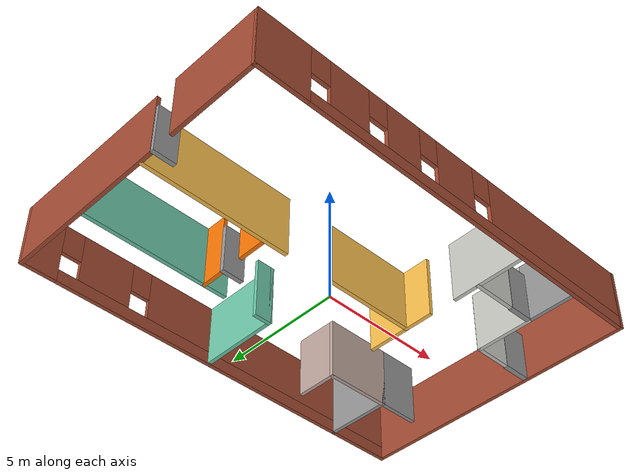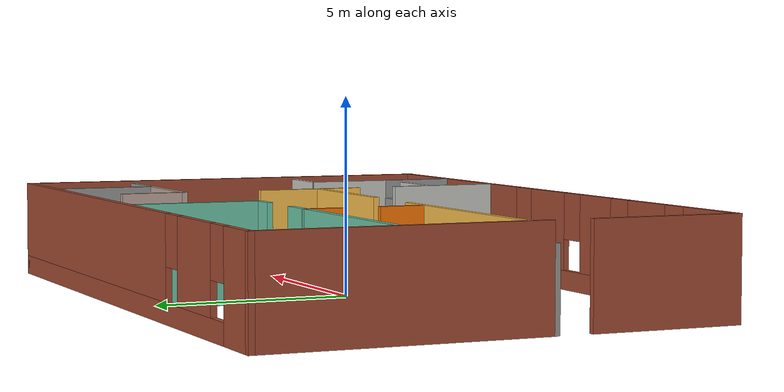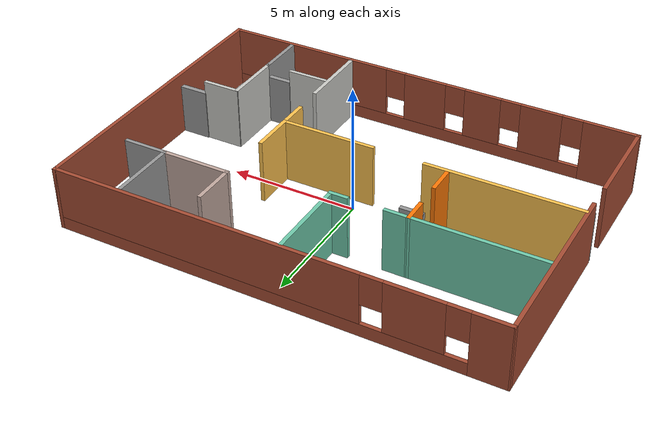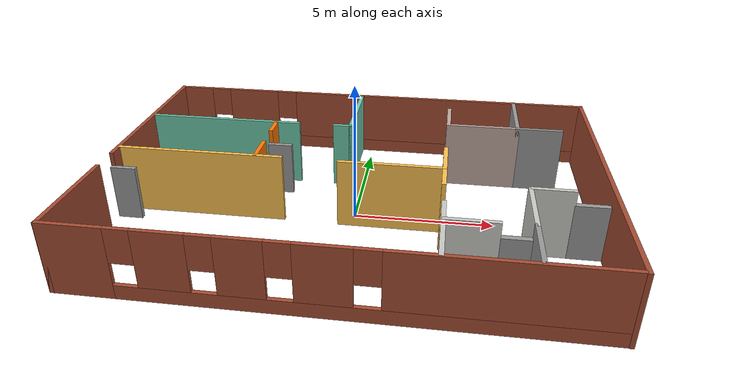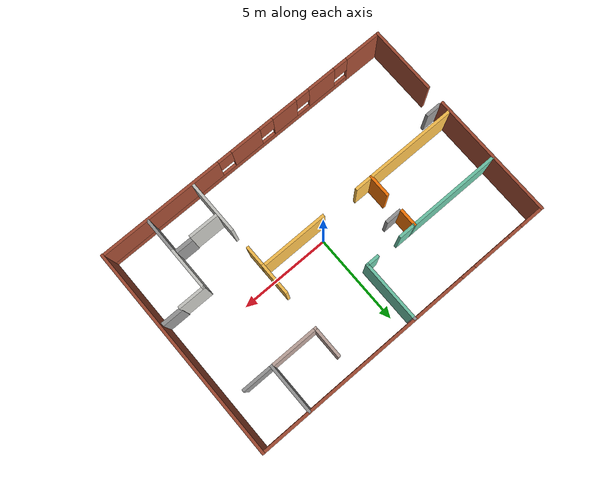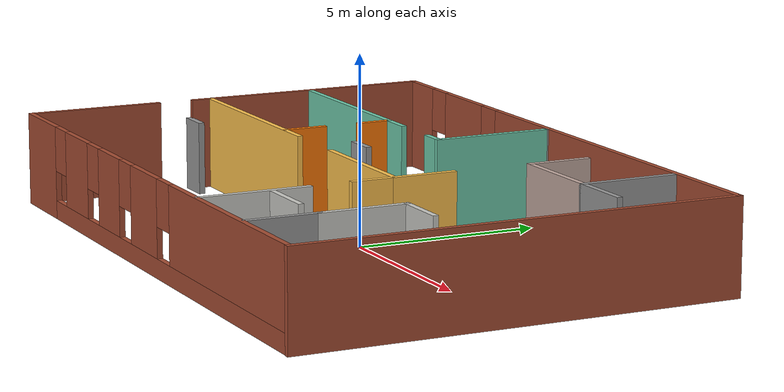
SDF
<?xml version='1.0'?>
<sdf version='1.6'>
  <model name='Office_Udacity'>
    <link name='Door_0'>
      <pose frame=''>-8.07861 -1.17997 0 0 -0 0</pose>
      <self_collide>0</self_collide>
      <enable_wind>0</enable_wind>
      <kinematic>0</kinematic>
      <visual name='Door_0_Visual'>
        <pose frame=''>0 0 1 0 -0 0</pose>
        <geometry>
          <box>
            <size>0.9 0.17 2</size>
          </box>
        </geometry>
        <material>
          <script>
            <uri>file://media/materials/scripts/gazebo.material</uri>
            <name>Gazebo/Grey</name>
          </script>
          <shader type='pixel'/>
        </material>
        <transparency>0</transparency>
        <cast_shadows>1</cast_shadows>
      </visual>
      <collision name='Door_0_Collision'>
        <laser_retro>0</laser_retro>
        <max_contacts>10</max_contacts>
        <pose frame=''>0 0 1 0 -0 0</pose>
        <geometry>
          <box>
            <size>0.9 0.17 2</size>
          </box>
        </geometry>
        <surface>
          <friction>
            <ode>
              <mu>1</mu>
              <mu2>1</mu2>
              <fdir1>0 0 0</fdir1>
              <slip1>0</slip1>
              <slip2>0</slip2>
            </ode>
            <torsional>
              <coefficient>1</coefficient>
              <patch_radius>0</patch_radius>
              <surface_radius>0</surface_radius>
              <use_patch_radius>1</use_patch_radius>
              <ode>
                <slip>0</slip>
              </ode>
            </torsional>
          </friction>
          <bounce>
            <restitution_coefficient>0</restitution_coefficient>
            <threshold>1e+06</threshold>
          </bounce>
          <contact>
            <collide_without_contact>0</collide_without_contact>
            <collide_without_contact_bitmask>1</collide_without_contact_bitmask>
            <collide_bitmask>1</collide_bitmask>
            <ode>
              <soft_cfm>0</soft_cfm>
              <soft_erp>0.2</soft_erp>
              <kp>1e+13</kp>
              <kd>1</kd>
              <max_vel>0.01</max_vel>
              <min_depth>0</min_depth>
            </ode>
            <bullet>
              <split_impulse>1</split_impulse>
              <split_impulse_penetration_threshold>-0.01</split_impulse_penetration_threshold>
              <soft_cfm>0</soft_cfm>
              <soft_erp>0.2</soft_erp>
              <kp>1e+13</kp>
              <kd>1</kd>
            </bullet>
          </contact>
        </surface>
      </collision>
    </link>
    <link name='Door_1'>
      <pose frame=''>-3.06619 1.513 0 0 -0 0.01009</pose>
      <self_collide>0</self_collide>
      <enable_wind>0</enable_wind>
      <kinematic>0</kinematic>
      <visual name='Door_1_Visual'>
        <pose frame=''>0 0 1 0 -0 0</pose>
        <geometry>
          <box>
            <size>0.9 0.17 2</size>
          </box>
        </geometry>
        <material>
          <script>
            <uri>file://media/materials/scripts/gazebo.material</uri>
            <name>Gazebo/Grey</name>
          </script>
          <shader type='pixel'/>
        </material>
        <transparency>0</transparency>
        <cast_shadows>1</cast_shadows>
      </visual>
      <collision name='Door_1_Collision'>
        <laser_retro>0</laser_retro>
        <max_contacts>10</max_contacts>
        <pose frame=''>0 0 1 0 -0 0</pose>
        <geometry>
          <box>
            <size>0.9 0.17 2</size>
          </box>
        </geometry>
        <surface>
          <friction>
            <ode>
              <mu>1</mu>
              <mu2>1</mu2>
              <fdir1>0 0 0</fdir1>
              <slip1>0</slip1>
              <slip2>0</slip2>
            </ode>
            <torsional>
              <coefficient>1</coefficient>
              <patch_radius>0</patch_radius>
              <surface_radius>0</surface_radius>
              <use_patch_radius>1</use_patch_radius>
              <ode>
                <slip>0</slip>
              </ode>
            </torsional>
          </friction>
          <bounce>
            <restitution_coefficient>0</restitution_coefficient>
            <threshold>1e+06</threshold>
          </bounce>
          <contact>
            <collide_without_contact>0</collide_without_contact>
            <collide_without_contact_bitmask>1</collide_without_contact_bitmask>
            <collide_bitmask>1</collide_bitmask>
            <ode>
              <soft_cfm>0</soft_cfm>
              <soft_erp>0.2</soft_erp>
              <kp>1e+13</kp>
              <kd>1</kd>
              <max_vel>0.01</max_vel>
              <min_depth>0</min_depth>
            </ode>
            <bullet>
              <split_impulse>1</split_impulse>
              <split_impulse_penetration_threshold>-0.01</split_impulse_penetration_threshold>
              <soft_cfm>0</soft_cfm>
              <soft_erp>0.2</soft_erp>
              <kp>1e+13</kp>
              <kd>1</kd>
            </bullet>
          </contact>
        </surface>
      </collision>
    </link>
    <link name='Door_5'>
      <pose frame=''>5.34472 -3.85243 0 0 -0 0</pose>
      <self_collide>0</self_collide>
      <enable_wind>0</enable_wind>
      <kinematic>0</kinematic>
      <visual name='Door_5_Visual'>
        <pose frame=''>0 0 1 0 -0 0</pose>
        <geometry>
          <box>
            <size>0.959661 0.2 2</size>
          </box>
        </geometry>
        <material>
          <script>
            <uri>file://media/materials/scripts/gazebo.material</uri>
            <name>Gazebo/Grey</name>
          </script>
          <shader type='pixel'/>
        </material>
        <transparency>0</transparency>
        <cast_shadows>1</cast_shadows>
      </visual>
      <collision name='Door_5_Collision'>
        <laser_retro>0</laser_retro>
        <max_contacts>10</max_contacts>
        <pose frame=''>0 0 1 0 -0 0</pose>
        <geometry>
          <box>
            <size>0.959661 0.2 2</size>
          </box>
        </geometry>
        <surface>
          <friction>
            <ode>
              <mu>1</mu>
              <mu2>1</mu2>
              <fdir1>0 0 0</fdir1>
              <slip1>0</slip1>
              <slip2>0</slip2>
            </ode>
            <torsional>
              <coefficient>1</coefficient>
              <patch_radius>0</patch_radius>
              <surface_radius>0</surface_radius>
              <use_patch_radius>1</use_patch_radius>
              <ode>
                <slip>0</slip>
              </ode>
            </torsional>
          </friction>
          <bounce>
            <restitution_coefficient>0</restitution_coefficient>
            <threshold>1e+06</threshold>
          </bounce>
          <contact>
            <collide_without_contact>0</collide_without_contact>
            <collide_without_contact_bitmask>1</collide_without_contact_bitmask>
            <collide_bitmask>1</collide_bitmask>
            <ode>
              <soft_cfm>0</soft_cfm>
              <soft_erp>0.2</soft_erp>
              <kp>1e+13</kp>
              <kd>1</kd>
              <max_vel>0.01</max_vel>
              <min_depth>0</min_depth>
            </ode>
            <bullet>
              <split_impulse>1</split_impulse>
              <split_impulse_penetration_threshold>-0.01</split_impulse_penetration_threshold>
              <soft_cfm>0</soft_cfm>
              <soft_erp>0.2</soft_erp>
              <kp>1e+13</kp>
              <kd>1</kd>
            </bullet>
          </contact>
        </surface>
      </collision>
    </link>
    <link name='Door_6'>
      <pose frame=''>7.84609 -1.59543 0 0 -0 0</pose>
      <self_collide>0</self_collide>
      <enable_wind>0</enable_wind>
      <kinematic>0</kinematic>
      <visual name='Door_6_Visual'>
        <pose frame=''>0 0 1 0 -0 0</pose>
        <geometry>
          <box>
            <size>1.1287 0.2 2</size>
          </box>
        </geometry>
        <material>
          <script>
            <uri>file://media/materials/scripts/gazebo.material</uri>
            <name>Gazebo/Grey</name>
          </script>
          <shader type='pixel'/>
        </material>
        <transparency>0</transparency>
        <cast_shadows>1</cast_shadows>
      </visual>
      <collision name='Door_6_Collision'>
        <laser_retro>0</laser_retro>
        <max_contacts>10</max_contacts>
        <pose frame=''>0 0 1 0 -0 0</pose>
        <geometry>
          <box>
            <size>1.1287 0.2 2</size>
          </box>
        </geometry>
        <surface>
          <friction>
            <ode>
              <mu>1</mu>
              <mu2>1</mu2>
              <fdir1>0 0 0</fdir1>
              <slip1>0</slip1>
              <slip2>0</slip2>
            </ode>
            <torsional>
              <coefficient>1</coefficient>
              <patch_radius>0</patch_radius>
              <surface_radius>0</surface_radius>
              <use_patch_radius>1</use_patch_radius>
              <ode>
                <slip>0</slip>
              </ode>
            </torsional>
          </friction>
          <bounce>
            <restitution_coefficient>0</restitution_coefficient>
            <threshold>1e+06</threshold>
          </bounce>
          <contact>
            <collide_without_contact>0</collide_without_contact>
            <collide_without_contact_bitmask>1</collide_without_contact_bitmask>
            <collide_bitmask>1</collide_bitmask>
            <ode>
              <soft_cfm>0</soft_cfm>
              <soft_erp>0.2</soft_erp>
              <kp>1e+13</kp>
              <kd>1</kd>
              <max_vel>0.01</max_vel>
              <min_depth>0</min_depth>
            </ode>
            <bullet>
              <split_impulse>1</split_impulse>
              <split_impulse_penetration_threshold>-0.01</split_impulse_penetration_threshold>
              <soft_cfm>0</soft_cfm>
              <soft_erp>0.2</soft_erp>
              <kp>1e+13</kp>
              <kd>1</kd>
            </bullet>
          </contact>
        </surface>
      </collision>
    </link>
    <link name='Wall_23'>
      <pose frame=''>-5.4726 -0.539 0 0 -0 0</pose>
      <self_collide>0</self_collide>
      <enable_wind>0</enable_wind>
      <kinematic>0</kinematic>
      <visual name='Wall_23_Visual'>
        <pose frame=''>0 0 1.25 0 -0 0</pose>
        <geometry>
          <box>
            <size>6 0.15 2.5</size>
          </box>
        </geometry>
        <material>
          <script>
            <uri>file://media/materials/scripts/gazebo.material</uri>
            <name>Gazebo/Grey</name>
          </script>
          <ambient>1 0.764706 0.305882 1</ambient>
          <shader type='pixel'/>
        </material>
        <meta>
          <layer>0</layer>
        </meta>
        <transparency>0</transparency>
        <cast_shadows>1</cast_shadows>
      </visual>
      <collision name='Wall_23_Collision'>
        <laser_retro>0</laser_retro>
        <max_contacts>10</max_contacts>
        <pose frame=''>0 0 1.25 0 -0 0</pose>
        <geometry>
          <box>
            <size>6 0.15 2.5</size>
          </box>
        </geometry>
        <surface>
          <friction>
            <ode>
              <mu>1</mu>
              <mu2>1</mu2>
              <fdir1>0 0 0</fdir1>
              <slip1>0</slip1>
              <slip2>0</slip2>
            </ode>
            <torsional>
              <coefficient>1</coefficient>
              <patch_radius>0</patch_radius>
              <surface_radius>0</surface_radius>
              <use_patch_radius>1</use_patch_radius>
              <ode>
                <slip>0</slip>
              </ode>
            </torsional>
          </friction>
          <bounce>
            <restitution_coefficient>0</restitution_coefficient>
            <threshold>1e+06</threshold>
          </bounce>
          <contact>
            <collide_without_contact>0</collide_without_contact>
            <collide_without_contact_bitmask>1</collide_without_contact_bitmask>
            <collide_bitmask>1</collide_bitmask>
            <ode>
              <soft_cfm>0</soft_cfm>
              <soft_erp>0.2</soft_erp>
              <kp>1e+13</kp>
              <kd>1</kd>
              <max_vel>0.01</max_vel>
              <min_depth>0</min_depth>
            </ode>
            <bullet>
              <split_impulse>1</split_impulse>
              <split_impulse_penetration_threshold>-0.01</split_impulse_penetration_threshold>
              <soft_cfm>0</soft_cfm>
              <soft_erp>0.2</soft_erp>
              <kp>1e+13</kp>
              <kd>1</kd>
            </bullet>
          </contact>
        </surface>
      </collision>
    </link>
    <link name='Wall_25'>
      <pose frame=''>-3.43548 0.030226 0 0 -0 1.5708</pose>
      <self_collide>0</self_collide>
      <enable_wind>0</enable_wind>
      <kinematic>0</kinematic>
      <visual name='Wall_25_Visual'>
        <pose frame=''>0 0 1.25 0 -0 0</pose>
        <geometry>
          <box>
            <size>1.25 0.15 2.5</size>
          </box>
        </geometry>
        <material>
          <script>
            <uri>file://media/materials/scripts/gazebo.material</uri>
            <name>Gazebo/Grey</name>
          </script>
          <ambient>0.996078 0.47451 0.0196078 1</ambient>
          <shader type='pixel'/>
        </material>
        <meta>
          <layer>0</layer>
        </meta>
        <transparency>0</transparency>
        <cast_shadows>1</cast_shadows>
      </visual>
      <collision name='Wall_25_Collision'>
        <laser_retro>0</laser_retro>
        <max_contacts>10</max_contacts>
        <pose frame=''>0 0 1.25 0 -0 0</pose>
        <geometry>
          <box>
            <size>1.25 0.15 2.5</size>
          </box>
        </geometry>
        <surface>
          <friction>
            <ode>
              <mu>1</mu>
              <mu2>1</mu2>
              <fdir1>0 0 0</fdir1>
              <slip1>0</slip1>
              <slip2>0</slip2>
            </ode>
            <torsional>
              <coefficient>1</coefficient>
              <patch_radius>0</patch_radius>
              <surface_radius>0</surface_radius>
              <use_patch_radius>1</use_patch_radius>
              <ode>
                <slip>0</slip>
              </ode>
            </torsional>
          </friction>
          <bounce>
            <restitution_coefficient>0</restitution_coefficient>
            <threshold>1e+06</threshold>
          </bounce>
          <contact>
            <collide_without_contact>0</collide_without_contact>
            <collide_without_contact_bitmask>1</collide_without_contact_bitmask>
            <collide_bitmask>1</collide_bitmask>
            <ode>
              <soft_cfm>0</soft_cfm>
              <soft_erp>0.2</soft_erp>
              <kp>1e+13</kp>
              <kd>1</kd>
              <max_vel>0.01</max_vel>
              <min_depth>0</min_depth>
            </ode>
            <bullet>
              <split_impulse>1</split_impulse>
              <split_impulse_penetration_threshold>-0.01</split_impulse_penetration_threshold>
              <soft_cfm>0</soft_cfm>
              <soft_erp>0.2</soft_erp>
              <kp>1e+13</kp>
              <kd>1</kd>
            </bullet>
          </contact>
        </surface>
      </collision>
    </link>
    <link name='Wall_27'>
      <pose frame=''>-3.43554 2.07794 0 0 -0 1.57094</pose>
      <self_collide>0</self_collide>
      <enable_wind>0</enable_wind>
      <kinematic>0</kinematic>
      <visual name='Wall_27_Visual'>
        <pose frame=''>0 0 1.25 0 -0 0</pose>
        <geometry>
          <box>
            <size>1 0.15 2.5</size>
          </box>
        </geometry>
        <material>
          <script>
            <uri>file://media/materials/scripts/gazebo.material</uri>
            <name>Gazebo/Grey</name>
          </script>
          <ambient>0.996078 0.47451 0.0196078 1</ambient>
          <shader type='pixel'/>
        </material>
        <meta>
          <layer>0</layer>
        </meta>
        <transparency>0</transparency>
        <cast_shadows>1</cast_shadows>
      </visual>
      <collision name='Wall_27_Collision'>
        <laser_retro>0</laser_retro>
        <max_contacts>10</max_contacts>
        <pose frame=''>0 0 1.25 0 -0 0</pose>
        <geometry>
          <box>
            <size>1 0.15 2.5</size>
          </box>
        </geometry>
        <surface>
          <friction>
            <ode>
              <mu>1</mu>
              <mu2>1</mu2>
              <fdir1>0 0 0</fdir1>
              <slip1>0</slip1>
              <slip2>0</slip2>
            </ode>
            <torsional>
              <coefficient>1</coefficient>
              <patch_radius>0</patch_radius>
              <surface_radius>0</surface_radius>
              <use_patch_radius>1</use_patch_radius>
              <ode>
                <slip>0</slip>
              </ode>
            </torsional>
          </friction>
          <bounce>
            <restitution_coefficient>0</restitution_coefficient>
            <threshold>1e+06</threshold>
          </bounce>
          <contact>
            <collide_without_contact>0</collide_without_contact>
            <collide_without_contact_bitmask>1</collide_without_contact_bitmask>
            <collide_bitmask>1</collide_bitmask>
            <ode>
              <soft_cfm>0</soft_cfm>
              <soft_erp>0.2</soft_erp>
              <kp>1e+13</kp>
              <kd>1</kd>
              <max_vel>0.01</max_vel>
              <min_depth>0</min_depth>
            </ode>
            <bullet>
              <split_impulse>1</split_impulse>
              <split_impulse_penetration_threshold>-0.01</split_impulse_penetration_threshold>
              <soft_cfm>0</soft_cfm>
              <soft_erp>0.2</soft_erp>
              <kp>1e+13</kp>
              <kd>1</kd>
            </bullet>
          </contact>
        </surface>
      </collision>
    </link>
    <link name='Wall_28'>
      <pose frame=''>-3.01054 2.50294 0 0 0 -0.000132</pose>
      <self_collide>0</self_collide>
      <enable_wind>0</enable_wind>
      <kinematic>0</kinematic>
      <visual name='Wall_28_Visual'>
        <pose frame=''>0 0 1.25 0 -0 0</pose>
        <geometry>
          <box>
            <size>1 0.15 2.5</size>
          </box>
        </geometry>
        <material>
          <script>
            <uri>file://media/materials/scripts/gazebo.material</uri>
            <name>Gazebo/Grey</name>
          </script>
          <ambient>0.435294 0.796078 0.67451 1</ambient>
          <shader type='pixel'/>
        </material>
        <meta>
          <layer>0</layer>
        </meta>
        <transparency>0</transparency>
        <cast_shadows>1</cast_shadows>
      </visual>
      <collision name='Wall_28_Collision'>
        <laser_retro>0</laser_retro>
        <max_contacts>10</max_contacts>
        <pose frame=''>0 0 1.25 0 -0 0</pose>
        <geometry>
          <box>
            <size>1 0.15 2.5</size>
          </box>
        </geometry>
        <surface>
          <friction>
            <ode>
              <mu>1</mu>
              <mu2>1</mu2>
              <fdir1>0 0 0</fdir1>
              <slip1>0</slip1>
              <slip2>0</slip2>
            </ode>
            <torsional>
              <coefficient>1</coefficient>
              <patch_radius>0</patch_radius>
              <surface_radius>0</surface_radius>
              <use_patch_radius>1</use_patch_radius>
              <ode>
                <slip>0</slip>
              </ode>
            </torsional>
          </friction>
          <bounce>
            <restitution_coefficient>0</restitution_coefficient>
            <threshold>1e+06</threshold>
          </bounce>
          <contact>
            <collide_without_contact>0</collide_without_contact>
            <collide_without_contact_bitmask>1</collide_without_contact_bitmask>
            <collide_bitmask>1</collide_bitmask>
            <ode>
              <soft_cfm>0</soft_cfm>
              <soft_erp>0.2</soft_erp>
              <kp>1e+13</kp>
              <kd>1</kd>
              <max_vel>0.01</max_vel>
              <min_depth>0</min_depth>
            </ode>
            <bullet>
              <split_impulse>1</split_impulse>
              <split_impulse_penetration_threshold>-0.01</split_impulse_penetration_threshold>
              <soft_cfm>0</soft_cfm>
              <soft_erp>0.2</soft_erp>
              <kp>1e+13</kp>
              <kd>1</kd>
            </bullet>
          </contact>
        </surface>
      </collision>
    </link>
    <link name='Wall_3'>
      <pose frame=''>0.009 5.8 0 0 -0 0</pose>
      <self_collide>0</self_collide>
      <enable_wind>0</enable_wind>
      <kinematic>0</kinematic>
      <visual name='Wall_3_Visual_0'>
        <pose frame=''>-7.84891 0 1.25 0 -0 0</pose>
        <geometry>
          <box>
            <size>1.40738 0.15 2.5</size>
          </box>
        </geometry>
        <material>
          <script>
            <uri>file://media/materials/scripts/gazebo.material</uri>
            <name>Gazebo/Bricks</name>
          </script>
          <ambient>1 1 1 1</ambient>
          <shader type='pixel'/>
        </material>
        <meta>
          <layer>0</layer>
        </meta>
        <transparency>0</transparency>
        <cast_shadows>1</cast_shadows>
      </visual>
      <visual name='Wall_3_Visual_1'>
        <pose frame=''>0.703691 0 0.25 0 -0 0</pose>
        <geometry>
          <box>
            <size>15.6978 0.15 0.5</size>
          </box>
        </geometry>
        <material>
          <script>
            <uri>file://media/materials/scripts/gazebo.material</uri>
            <name>Gazebo/Bricks</name>
          </script>
          <ambient>1 1 1 1</ambient>
          <shader type='pixel'/>
        </material>
        <meta>
          <layer>0</layer>
        </meta>
        <transparency>0</transparency>
        <cast_shadows>1</cast_shadows>
      </visual>
      <visual name='Wall_3_Visual_2'>
        <pose frame=''>-5.2807 0 1.5 0 -0 0</pose>
        <geometry>
          <box>
            <size>2.12904 0.15 2</size>
          </box>
        </geometry>
        <material>
          <script>
            <uri>file://media/materials/scripts/gazebo.material</uri>
            <name>Gazebo/Bricks</name>
          </script>
          <ambient>1 1 1 1</ambient>
          <shader type='pixel'/>
        </material>
        <meta>
          <layer>0</layer>
        </meta>
        <transparency>0</transparency>
        <cast_shadows>1</cast_shadows>
      </visual>
      <visual name='Wall_3_Visual_3'>
        <pose frame=''>2.56821 0 1.5 0 -0 0</pose>
        <geometry>
          <box>
            <size>11.9688 0.15 2</size>
          </box>
        </geometry>
        <material>
          <script>
            <uri>file://media/materials/scripts/gazebo.material</uri>
            <name>Gazebo/Bricks</name>
          </script>
          <ambient>1 1 1 1</ambient>
          <shader type='pixel'/>
        </material>
        <meta>
          <layer>0</layer>
        </meta>
        <transparency>0</transparency>
        <cast_shadows>1</cast_shadows>
      </visual>
      <visual name='Wall_3_Visual_4'>
        <pose frame=''>-6.74522 0 1.9 0 -0 0</pose>
        <geometry>
          <box>
            <size>0.8 0.15 1.2</size>
          </box>
        </geometry>
        <material>
          <script>
            <uri>file://media/materials/scripts/gazebo.material</uri>
            <name>Gazebo/Bricks</name>
          </script>
          <ambient>1 1 1 1</ambient>
          <shader type='pixel'/>
        </material>
        <meta>
          <layer>0</layer>
        </meta>
        <transparency>0</transparency>
        <cast_shadows>1</cast_shadows>
      </visual>
      <visual name='Wall_3_Visual_5'>
        <pose frame=''>-3.81618 0 1.9 0 -0 0</pose>
        <geometry>
          <box>
            <size>0.8 0.15 1.2</size>
          </box>
        </geometry>
        <material>
          <script>
            <uri>file://media/materials/scripts/gazebo.material</uri>
            <name>Gazebo/Bricks</name>
          </script>
          <ambient>1 1 1 1</ambient>
          <shader type='pixel'/>
        </material>
        <meta>
          <layer>0</layer>
        </meta>
        <transparency>0</transparency>
        <cast_shadows>1</cast_shadows>
      </visual>
      <collision name='Wall_3_Collision_0'>
        <laser_retro>0</laser_retro>
        <max_contacts>10</max_contacts>
        <pose frame=''>-7.84891 0 1.25 0 -0 0</pose>
        <geometry>
          <box>
            <size>1.40738 0.15 2.5</size>
          </box>
        </geometry>
        <surface>
          <friction>
            <ode>
              <mu>1</mu>
              <mu2>1</mu2>
              <fdir1>0 0 0</fdir1>
              <slip1>0</slip1>
              <slip2>0</slip2>
            </ode>
            <torsional>
              <coefficient>1</coefficient>
              <patch_radius>0</patch_radius>
              <surface_radius>0</surface_radius>
              <use_patch_radius>1</use_patch_radius>
              <ode>
                <slip>0</slip>
              </ode>
            </torsional>
          </friction>
          <bounce>
            <restitution_coefficient>0</restitution_coefficient>
            <threshold>1e+06</threshold>
          </bounce>
          <contact>
            <collide_without_contact>0</collide_without_contact>
            <collide_without_contact_bitmask>1</collide_without_contact_bitmask>
            <collide_bitmask>1</collide_bitmask>
            <ode>
              <soft_cfm>0</soft_cfm>
              <soft_erp>0.2</soft_erp>
              <kp>1e+13</kp>
              <kd>1</kd>
              <max_vel>0.01</max_vel>
              <min_depth>0</min_depth>
            </ode>
            <bullet>
              <split_impulse>1</split_impulse>
              <split_impulse_penetration_threshold>-0.01</split_impulse_penetration_threshold>
              <soft_cfm>0</soft_cfm>
              <soft_erp>0.2</soft_erp>
              <kp>1e+13</kp>
              <kd>1</kd>
            </bullet>
          </contact>
        </surface>
      </collision>
      <collision name='Wall_3_Collision_1'>
        <laser_retro>0</laser_retro>
        <max_contacts>10</max_contacts>
        <pose frame=''>0.703691 0 0.25 0 -0 0</pose>
        <geometry>
          <box>
            <size>15.6978 0.15 0.5</size>
          </box>
        </geometry>
        <surface>
          <friction>
            <ode>
              <mu>1</mu>
              <mu2>1</mu2>
              <fdir1>0 0 0</fdir1>
              <slip1>0</slip1>
              <slip2>0</slip2>
            </ode>
            <torsional>
              <coefficient>1</coefficient>
              <patch_radius>0</patch_radius>
              <surface_radius>0</surface_radius>
              <use_patch_radius>1</use_patch_radius>
              <ode>
                <slip>0</slip>
              </ode>
            </torsional>
          </friction>
          <bounce>
            <restitution_coefficient>0</restitution_coefficient>
            <threshold>1e+06</threshold>
          </bounce>
          <contact>
            <collide_without_contact>0</collide_without_contact>
            <collide_without_contact_bitmask>1</collide_without_contact_bitmask>
            <collide_bitmask>1</collide_bitmask>
            <ode>
              <soft_cfm>0</soft_cfm>
              <soft_erp>0.2</soft_erp>
              <kp>1e+13</kp>
              <kd>1</kd>
              <max_vel>0.01</max_vel>
              <min_depth>0</min_depth>
            </ode>
            <bullet>
              <split_impulse>1</split_impulse>
              <split_impulse_penetration_threshold>-0.01</split_impulse_penetration_threshold>
              <soft_cfm>0</soft_cfm>
              <soft_erp>0.2</soft_erp>
              <kp>1e+13</kp>
              <kd>1</kd>
            </bullet>
          </contact>
        </surface>
      </collision>
      <collision name='Wall_3_Collision_2'>
        <laser_retro>0</laser_retro>
        <max_contacts>10</max_contacts>
        <pose frame=''>-5.2807 0 1.5 0 -0 0</pose>
        <geometry>
          <box>
            <size>2.12904 0.15 2</size>
          </box>
        </geometry>
        <surface>
          <friction>
            <ode>
              <mu>1</mu>
              <mu2>1</mu2>
              <fdir1>0 0 0</fdir1>
              <slip1>0</slip1>
              <slip2>0</slip2>
            </ode>
            <torsional>
              <coefficient>1</coefficient>
              <patch_radius>0</patch_radius>
              <surface_radius>0</surface_radius>
              <use_patch_radius>1</use_patch_radius>
              <ode>
                <slip>0</slip>
              </ode>
            </torsional>
          </friction>
          <bounce>
            <restitution_coefficient>0</restitution_coefficient>
            <threshold>1e+06</threshold>
          </bounce>
          <contact>
            <collide_without_contact>0</collide_without_contact>
            <collide_without_contact_bitmask>1</collide_without_contact_bitmask>
            <collide_bitmask>1</collide_bitmask>
            <ode>
              <soft_cfm>0</soft_cfm>
              <soft_erp>0.2</soft_erp>
              <kp>1e+13</kp>
              <kd>1</kd>
              <max_vel>0.01</max_vel>
              <min_depth>0</min_depth>
            </ode>
            <bullet>
              <split_impulse>1</split_impulse>
              <split_impulse_penetration_threshold>-0.01</split_impulse_penetration_threshold>
              <soft_cfm>0</soft_cfm>
              <soft_erp>0.2</soft_erp>
              <kp>1e+13</kp>
              <kd>1</kd>
            </bullet>
          </contact>
        </surface>
      </collision>
      <collision name='Wall_3_Collision_3'>
        <laser_retro>0</laser_retro>
        <max_contacts>10</max_contacts>
        <pose frame=''>2.56821 0 1.5 0 -0 0</pose>
        <geometry>
          <box>
            <size>11.9688 0.15 2</size>
          </box>
        </geometry>
        <surface>
          <friction>
            <ode>
              <mu>1</mu>
              <mu2>1</mu2>
              <fdir1>0 0 0</fdir1>
              <slip1>0</slip1>
              <slip2>0</slip2>
            </ode>
            <torsional>
              <coefficient>1</coefficient>
              <patch_radius>0</patch_radius>
              <surface_radius>0</surface_radius>
              <use_patch_radius>1</use_patch_radius>
              <ode>
                <slip>0</slip>
              </ode>
            </torsional>
          </friction>
          <bounce>
            <restitution_coefficient>0</restitution_coefficient>
            <threshold>1e+06</threshold>
          </bounce>
          <contact>
            <collide_without_contact>0</collide_without_contact>
            <collide_without_contact_bitmask>1</collide_without_contact_bitmask>
            <collide_bitmask>1</collide_bitmask>
            <ode>
              <soft_cfm>0</soft_cfm>
              <soft_erp>0.2</soft_erp>
              <kp>1e+13</kp>
              <kd>1</kd>
              <max_vel>0.01</max_vel>
              <min_depth>0</min_depth>
            </ode>
            <bullet>
              <split_impulse>1</split_impulse>
              <split_impulse_penetration_threshold>-0.01</split_impulse_penetration_threshold>
              <soft_cfm>0</soft_cfm>
              <soft_erp>0.2</soft_erp>
              <kp>1e+13</kp>
              <kd>1</kd>
            </bullet>
          </contact>
        </surface>
      </collision>
      <collision name='Wall_3_Collision_4'>
        <laser_retro>0</laser_retro>
        <max_contacts>10</max_contacts>
        <pose frame=''>-6.74522 0 1.9 0 -0 0</pose>
        <geometry>
          <box>
            <size>0.8 0.15 1.2</size>
          </box>
        </geometry>
        <surface>
          <friction>
            <ode>
              <mu>1</mu>
              <mu2>1</mu2>
              <fdir1>0 0 0</fdir1>
              <slip1>0</slip1>
              <slip2>0</slip2>
            </ode>
            <torsional>
              <coefficient>1</coefficient>
              <patch_radius>0</patch_radius>
              <surface_radius>0</surface_radius>
              <use_patch_radius>1</use_patch_radius>
              <ode>
                <slip>0</slip>
              </ode>
            </torsional>
          </friction>
          <bounce>
            <restitution_coefficient>0</restitution_coefficient>
            <threshold>1e+06</threshold>
          </bounce>
          <contact>
            <collide_without_contact>0</collide_without_contact>
            <collide_without_contact_bitmask>1</collide_without_contact_bitmask>
            <collide_bitmask>1</collide_bitmask>
            <ode>
              <soft_cfm>0</soft_cfm>
              <soft_erp>0.2</soft_erp>
              <kp>1e+13</kp>
              <kd>1</kd>
              <max_vel>0.01</max_vel>
              <min_depth>0</min_depth>
            </ode>
            <bullet>
              <split_impulse>1</split_impulse>
              <split_impulse_penetration_threshold>-0.01</split_impulse_penetration_threshold>
              <soft_cfm>0</soft_cfm>
              <soft_erp>0.2</soft_erp>
              <kp>1e+13</kp>
              <kd>1</kd>
            </bullet>
          </contact>
        </surface>
      </collision>
      <collision name='Wall_3_Collision_5'>
        <laser_retro>0</laser_retro>
        <max_contacts>10</max_contacts>
        <pose frame=''>-3.81618 0 1.9 0 -0 0</pose>
        <geometry>
          <box>
            <size>0.8 0.15 1.2</size>
          </box>
        </geometry>
        <surface>
          <friction>
            <ode>
              <mu>1</mu>
              <mu2>1</mu2>
              <fdir1>0 0 0</fdir1>
              <slip1>0</slip1>
              <slip2>0</slip2>
            </ode>
            <torsional>
              <coefficient>1</coefficient>
              <patch_radius>0</patch_radius>
              <surface_radius>0</surface_radius>
              <use_patch_radius>1</use_patch_radius>
              <ode>
                <slip>0</slip>
              </ode>
            </torsional>
          </friction>
          <bounce>
            <restitution_coefficient>0</restitution_coefficient>
            <threshold>1e+06</threshold>
          </bounce>
          <contact>
            <collide_without_contact>0</collide_without_contact>
            <collide_without_contact_bitmask>1</collide_without_contact_bitmask>
            <collide_bitmask>1</collide_bitmask>
            <ode>
              <soft_cfm>0</soft_cfm>
              <soft_erp>0.2</soft_erp>
              <kp>1e+13</kp>
              <kd>1</kd>
              <max_vel>0.01</max_vel>
              <min_depth>0</min_depth>
            </ode>
            <bullet>
              <split_impulse>1</split_impulse>
              <split_impulse_penetration_threshold>-0.01</split_impulse_penetration_threshold>
              <soft_cfm>0</soft_cfm>
              <soft_erp>0.2</soft_erp>
              <kp>1e+13</kp>
              <kd>1</kd>
            </bullet>
          </contact>
        </surface>
      </collision>
    </link>
    <link name='Wall_30'>
      <pose frame=''>-0.821601 2.507 0 0 -0 0</pose>
      <self_collide>0</self_collide>
      <enable_wind>0</enable_wind>
      <kinematic>0</kinematic>
      <visual name='Wall_30_Visual'>
        <pose frame=''>0 0 1.25 0 -0 0</pose>
        <geometry>
          <box>
            <size>0.75 0.15 2.5</size>
          </box>
        </geometry>
        <material>
          <script>
            <uri>file://media/materials/scripts/gazebo.material</uri>
            <name>Gazebo/Grey</name>
          </script>
          <ambient>0.435294 0.796078 0.67451 1</ambient>
          <shader type='pixel'/>
        </material>
        <meta>
          <layer>0</layer>
        </meta>
        <transparency>0</transparency>
        <cast_shadows>1</cast_shadows>
      </visual>
      <collision name='Wall_30_Collision'>
        <laser_retro>0</laser_retro>
        <max_contacts>10</max_contacts>
        <pose frame=''>0 0 1.25 0 -0 0</pose>
        <geometry>
          <box>
            <size>0.75 0.15 2.5</size>
          </box>
        </geometry>
        <surface>
          <friction>
            <ode>
              <mu>1</mu>
              <mu2>1</mu2>
              <fdir1>0 0 0</fdir1>
              <slip1>0</slip1>
              <slip2>0</slip2>
            </ode>
            <torsional>
              <coefficient>1</coefficient>
              <patch_radius>0</patch_radius>
              <surface_radius>0</surface_radius>
              <use_patch_radius>1</use_patch_radius>
              <ode>
                <slip>0</slip>
              </ode>
            </torsional>
          </friction>
          <bounce>
            <restitution_coefficient>0</restitution_coefficient>
            <threshold>1e+06</threshold>
          </bounce>
          <contact>
            <collide_without_contact>0</collide_without_contact>
            <collide_without_contact_bitmask>1</collide_without_contact_bitmask>
            <collide_bitmask>1</collide_bitmask>
            <ode>
              <soft_cfm>0</soft_cfm>
              <soft_erp>0.2</soft_erp>
              <kp>1e+13</kp>
              <kd>1</kd>
              <max_vel>0.01</max_vel>
              <min_depth>0</min_depth>
            </ode>
            <bullet>
              <split_impulse>1</split_impulse>
              <split_impulse_penetration_threshold>-0.01</split_impulse_penetration_threshold>
              <soft_cfm>0</soft_cfm>
              <soft_erp>0.2</soft_erp>
              <kp>1e+13</kp>
              <kd>1</kd>
            </bullet>
          </contact>
        </surface>
      </collision>
    </link>
    <link name='Wall_31'>
      <pose frame=''>-0.521601 4.132 0 0 -0 1.5708</pose>
      <self_collide>0</self_collide>
      <enable_wind>0</enable_wind>
      <kinematic>0</kinematic>
      <visual name='Wall_31_Visual'>
        <pose frame=''>0 0 1.25 0 -0 0</pose>
        <geometry>
          <box>
            <size>3.4 0.15 2.5</size>
          </box>
        </geometry>
        <material>
          <script>
            <uri>file://media/materials/scripts/gazebo.material</uri>
            <name>Gazebo/Grey</name>
          </script>
          <ambient>0.435294 0.796078 0.67451 1</ambient>
          <shader type='pixel'/>
        </material>
        <meta>
          <layer>0</layer>
        </meta>
        <transparency>0</transparency>
        <cast_shadows>1</cast_shadows>
      </visual>
      <collision name='Wall_31_Collision'>
        <laser_retro>0</laser_retro>
        <max_contacts>10</max_contacts>
        <pose frame=''>0 0 1.25 0 -0 0</pose>
        <geometry>
          <box>
            <size>3.4 0.15 2.5</size>
          </box>
        </geometry>
        <surface>
          <friction>
            <ode>
              <mu>1</mu>
              <mu2>1</mu2>
              <fdir1>0 0 0</fdir1>
              <slip1>0</slip1>
              <slip2>0</slip2>
            </ode>
            <torsional>
              <coefficient>1</coefficient>
              <patch_radius>0</patch_radius>
              <surface_radius>0</surface_radius>
              <use_patch_radius>1</use_patch_radius>
              <ode>
                <slip>0</slip>
              </ode>
            </torsional>
          </friction>
          <bounce>
            <restitution_coefficient>0</restitution_coefficient>
            <threshold>1e+06</threshold>
          </bounce>
          <contact>
            <collide_without_contact>0</collide_without_contact>
            <collide_without_contact_bitmask>1</collide_without_contact_bitmask>
            <collide_bitmask>1</collide_bitmask>
            <ode>
              <soft_cfm>0</soft_cfm>
              <soft_erp>0.2</soft_erp>
              <kp>1e+13</kp>
              <kd>1</kd>
              <max_vel>0.01</max_vel>
              <min_depth>0</min_depth>
            </ode>
            <bullet>
              <split_impulse>1</split_impulse>
              <split_impulse_penetration_threshold>-0.01</split_impulse_penetration_threshold>
              <soft_cfm>0</soft_cfm>
              <soft_erp>0.2</soft_erp>
              <kp>1e+13</kp>
              <kd>1</kd>
            </bullet>
          </contact>
        </surface>
      </collision>
    </link>
    <link name='Wall_32'>
      <pose frame=''>-0.521601 5.757 0 0 -0 0</pose>
      <self_collide>0</self_collide>
      <enable_wind>0</enable_wind>
      <kinematic>0</kinematic>
      <visual name='Wall_32_Visual'>
        <pose frame=''>0 0 1.25 0 -0 0</pose>
        <geometry>
          <box>
            <size>0.15 0.15 2.5</size>
          </box>
        </geometry>
        <material>
          <script>
            <uri>file://media/materials/scripts/gazebo.material</uri>
            <name>Gazebo/Grey</name>
          </script>
          <ambient>1 1 1 1</ambient>
          <shader type='pixel'/>
        </material>
        <meta>
          <layer>0</layer>
        </meta>
        <transparency>0</transparency>
        <cast_shadows>1</cast_shadows>
      </visual>
      <collision name='Wall_32_Collision'>
        <laser_retro>0</laser_retro>
        <max_contacts>10</max_contacts>
        <pose frame=''>0 0 1.25 0 -0 0</pose>
        <geometry>
          <box>
            <size>0.15 0.15 2.5</size>
          </box>
        </geometry>
        <surface>
          <friction>
            <ode>
              <mu>1</mu>
              <mu2>1</mu2>
              <fdir1>0 0 0</fdir1>
              <slip1>0</slip1>
              <slip2>0</slip2>
            </ode>
            <torsional>
              <coefficient>1</coefficient>
              <patch_radius>0</patch_radius>
              <surface_radius>0</surface_radius>
              <use_patch_radius>1</use_patch_radius>
              <ode>
                <slip>0</slip>
              </ode>
            </torsional>
          </friction>
          <bounce>
            <restitution_coefficient>0</restitution_coefficient>
            <threshold>1e+06</threshold>
          </bounce>
          <contact>
            <collide_without_contact>0</collide_without_contact>
            <collide_without_contact_bitmask>1</collide_without_contact_bitmask>
            <collide_bitmask>1</collide_bitmask>
            <ode>
              <soft_cfm>0</soft_cfm>
              <soft_erp>0.2</soft_erp>
              <kp>1e+13</kp>
              <kd>1</kd>
              <max_vel>0.01</max_vel>
              <min_depth>0</min_depth>
            </ode>
            <bullet>
              <split_impulse>1</split_impulse>
              <split_impulse_penetration_threshold>-0.01</split_impulse_penetration_threshold>
              <soft_cfm>0</soft_cfm>
              <soft_erp>0.2</soft_erp>
              <kp>1e+13</kp>
              <kd>1</kd>
            </bullet>
          </contact>
        </surface>
      </collision>
    </link>
    <link name='Wall_34'>
      <pose frame=''>-5.9106 2.503 0 0 -0 3.14159</pose>
      <self_collide>0</self_collide>
      <enable_wind>0</enable_wind>
      <kinematic>0</kinematic>
      <visual name='Wall_34_Visual'>
        <pose frame=''>0 0 1.25 0 -0 0</pose>
        <geometry>
          <box>
            <size>5.1 0.15 2.5</size>
          </box>
        </geometry>
        <material>
          <script>
            <uri>file://media/materials/scripts/gazebo.material</uri>
            <name>Gazebo/Grey</name>
          </script>
          <ambient>0.435294 0.796078 0.67451 1</ambient>
          <shader type='pixel'/>
        </material>
        <meta>
          <layer>0</layer>
        </meta>
        <transparency>0</transparency>
        <cast_shadows>1</cast_shadows>
      </visual>
      <collision name='Wall_34_Collision'>
        <laser_retro>0</laser_retro>
        <max_contacts>10</max_contacts>
        <pose frame=''>0 0 1.25 0 -0 0</pose>
        <geometry>
          <box>
            <size>5.1 0.15 2.5</size>
          </box>
        </geometry>
        <surface>
          <friction>
            <ode>
              <mu>1</mu>
              <mu2>1</mu2>
              <fdir1>0 0 0</fdir1>
              <slip1>0</slip1>
              <slip2>0</slip2>
            </ode>
            <torsional>
              <coefficient>1</coefficient>
              <patch_radius>0</patch_radius>
              <surface_radius>0</surface_radius>
              <use_patch_radius>1</use_patch_radius>
              <ode>
                <slip>0</slip>
              </ode>
            </torsional>
          </friction>
          <bounce>
            <restitution_coefficient>0</restitution_coefficient>
            <threshold>1e+06</threshold>
          </bounce>
          <contact>
            <collide_without_contact>0</collide_without_contact>
            <collide_without_contact_bitmask>1</collide_without_contact_bitmask>
            <collide_bitmask>1</collide_bitmask>
            <ode>
              <soft_cfm>0</soft_cfm>
              <soft_erp>0.2</soft_erp>
              <kp>1e+13</kp>
              <kd>1</kd>
              <max_vel>0.01</max_vel>
              <min_depth>0</min_depth>
            </ode>
            <bullet>
              <split_impulse>1</split_impulse>
              <split_impulse_penetration_threshold>-0.01</split_impulse_penetration_threshold>
              <soft_cfm>0</soft_cfm>
              <soft_erp>0.2</soft_erp>
              <kp>1e+13</kp>
              <kd>1</kd>
            </bullet>
          </contact>
        </surface>
      </collision>
    </link>
    <link name='Wall_36'>
      <pose frame=''>5.86992 -4.76879 0 0 -0 1.5708</pose>
      <self_collide>0</self_collide>
      <enable_wind>0</enable_wind>
      <kinematic>0</kinematic>
      <visual name='Wall_36_Visual'>
        <pose frame=''>0 0 1.25 0 -0 0</pose>
        <geometry>
          <box>
            <size>2 0.15 2.5</size>
          </box>
        </geometry>
        <material>
          <script>
            <uri>file://media/materials/scripts/gazebo.material</uri>
            <name>Gazebo/Grey</name>
          </script>
          <ambient>1 1 1 1</ambient>
          <shader type='pixel'/>
        </material>
        <meta>
          <layer>0</layer>
        </meta>
        <transparency>0</transparency>
        <cast_shadows>1</cast_shadows>
      </visual>
      <collision name='Wall_36_Collision'>
        <laser_retro>0</laser_retro>
        <max_contacts>10</max_contacts>
        <pose frame=''>0 0 1.25 0 -0 0</pose>
        <geometry>
          <box>
            <size>2 0.15 2.5</size>
          </box>
        </geometry>
        <surface>
          <friction>
            <ode>
              <mu>1</mu>
              <mu2>1</mu2>
              <fdir1>0 0 0</fdir1>
              <slip1>0</slip1>
              <slip2>0</slip2>
            </ode>
            <torsional>
              <coefficient>1</coefficient>
              <patch_radius>0</patch_radius>
              <surface_radius>0</surface_radius>
              <use_patch_radius>1</use_patch_radius>
              <ode>
                <slip>0</slip>
              </ode>
            </torsional>
          </friction>
          <bounce>
            <restitution_coefficient>0</restitution_coefficient>
            <threshold>1e+06</threshold>
          </bounce>
          <contact>
            <collide_without_contact>0</collide_without_contact>
            <collide_without_contact_bitmask>1</collide_without_contact_bitmask>
            <collide_bitmask>1</collide_bitmask>
            <ode>
              <soft_cfm>0</soft_cfm>
              <soft_erp>0.2</soft_erp>
              <kp>1e+13</kp>
              <kd>1</kd>
              <max_vel>0.01</max_vel>
              <min_depth>0</min_depth>
            </ode>
            <bullet>
              <split_impulse>1</split_impulse>
              <split_impulse_penetration_threshold>-0.01</split_impulse_penetration_threshold>
              <soft_cfm>0</soft_cfm>
              <soft_erp>0.2</soft_erp>
              <kp>1e+13</kp>
              <kd>1</kd>
            </bullet>
          </contact>
        </surface>
      </collision>
    </link>
    <link name='Wall_42'>
      <pose frame=''>1.34487 -0.590852 0 0 -0 0</pose>
      <self_collide>0</self_collide>
      <enable_wind>0</enable_wind>
      <kinematic>0</kinematic>
      <visual name='Wall_42_Visual'>
        <pose frame=''>0 0 1.25 0 -0 0</pose>
        <geometry>
          <box>
            <size>3.75 0.15 2.5</size>
          </box>
        </geometry>
        <material>
          <script>
            <uri>file://media/materials/scripts/gazebo.material</uri>
            <name>Gazebo/Grey</name>
          </script>
          <ambient>1 0.764706 0.305882 1</ambient>
          <shader type='pixel'/>
        </material>
        <meta>
          <layer>0</layer>
        </meta>
        <transparency>0</transparency>
        <cast_shadows>1</cast_shadows>
      </visual>
      <collision name='Wall_42_Collision'>
        <laser_retro>0</laser_retro>
        <max_contacts>10</max_contacts>
        <pose frame=''>0 0 1.25 0 -0 0</pose>
        <geometry>
          <box>
            <size>3.75 0.15 2.5</size>
          </box>
        </geometry>
        <surface>
          <friction>
            <ode>
              <mu>1</mu>
              <mu2>1</mu2>
              <fdir1>0 0 0</fdir1>
              <slip1>0</slip1>
              <slip2>0</slip2>
            </ode>
            <torsional>
              <coefficient>1</coefficient>
              <patch_radius>0</patch_radius>
              <surface_radius>0</surface_radius>
              <use_patch_radius>1</use_patch_radius>
              <ode>
                <slip>0</slip>
              </ode>
            </torsional>
          </friction>
          <bounce>
            <restitution_coefficient>0</restitution_coefficient>
            <threshold>1e+06</threshold>
          </bounce>
          <contact>
            <collide_without_contact>0</collide_without_contact>
            <collide_without_contact_bitmask>1</collide_without_contact_bitmask>
            <collide_bitmask>1</collide_bitmask>
            <ode>
              <soft_cfm>0</soft_cfm>
              <soft_erp>0.2</soft_erp>
              <kp>1e+13</kp>
              <kd>1</kd>
              <max_vel>0.01</max_vel>
              <min_depth>0</min_depth>
            </ode>
            <bullet>
              <split_impulse>1</split_impulse>
              <split_impulse_penetration_threshold>-0.01</split_impulse_penetration_threshold>
              <soft_cfm>0</soft_cfm>
              <soft_erp>0.2</soft_erp>
              <kp>1e+13</kp>
              <kd>1</kd>
            </bullet>
          </contact>
        </surface>
      </collision>
    </link>
    <link name='Wall_43'>
      <pose frame=''>3.14487 -1.14085 0 0 0 -1.5708</pose>
      <self_collide>0</self_collide>
      <enable_wind>0</enable_wind>
      <kinematic>0</kinematic>
      <visual name='Wall_43_Visual'>
        <pose frame=''>0 0 1.25 0 -0 0</pose>
        <geometry>
          <box>
            <size>1.25 0.15 2.5</size>
          </box>
        </geometry>
        <material>
          <script>
            <uri>file://media/materials/scripts/gazebo.material</uri>
            <name>Gazebo/Grey</name>
          </script>
          <ambient>1 0.764706 0.305882 1</ambient>
          <shader type='pixel'/>
        </material>
        <meta>
          <layer>0</layer>
        </meta>
        <transparency>0</transparency>
        <cast_shadows>1</cast_shadows>
      </visual>
      <collision name='Wall_43_Collision'>
        <laser_retro>0</laser_retro>
        <max_contacts>10</max_contacts>
        <pose frame=''>0 0 1.25 0 -0 0</pose>
        <geometry>
          <box>
            <size>1.25 0.15 2.5</size>
          </box>
        </geometry>
        <surface>
          <friction>
            <ode>
              <mu>1</mu>
              <mu2>1</mu2>
              <fdir1>0 0 0</fdir1>
              <slip1>0</slip1>
              <slip2>0</slip2>
            </ode>
            <torsional>
              <coefficient>1</coefficient>
              <patch_radius>0</patch_radius>
              <surface_radius>0</surface_radius>
              <use_patch_radius>1</use_patch_radius>
              <ode>
                <slip>0</slip>
              </ode>
            </torsional>
          </friction>
          <bounce>
            <restitution_coefficient>0</restitution_coefficient>
            <threshold>1e+06</threshold>
          </bounce>
          <contact>
            <collide_without_contact>0</collide_without_contact>
            <collide_without_contact_bitmask>1</collide_without_contact_bitmask>
            <collide_bitmask>1</collide_bitmask>
            <ode>
              <soft_cfm>0</soft_cfm>
              <soft_erp>0.2</soft_erp>
              <kp>1e+13</kp>
              <kd>1</kd>
              <max_vel>0.01</max_vel>
              <min_depth>0</min_depth>
            </ode>
            <bullet>
              <split_impulse>1</split_impulse>
              <split_impulse_penetration_threshold>-0.01</split_impulse_penetration_threshold>
              <soft_cfm>0</soft_cfm>
              <soft_erp>0.2</soft_erp>
              <kp>1e+13</kp>
              <kd>1</kd>
            </bullet>
          </contact>
        </surface>
      </collision>
    </link>
    <link name='Wall_47'>
      <pose frame=''>3.17852 -4.30533 0 0 0 -1.5708</pose>
      <self_collide>0</self_collide>
      <enable_wind>0</enable_wind>
      <kinematic>0</kinematic>
      <visual name='Wall_47_Visual'>
        <pose frame=''>0 0 1.25 0 -0 0</pose>
        <geometry>
          <box>
            <size>3 0.15 2.5</size>
          </box>
        </geometry>
        <material>
          <script>
            <uri>file://media/materials/scripts/gazebo.material</uri>
            <name>Gazebo/CeilingTiled</name>
          </script>
          <ambient>1 1 1 1</ambient>
          <shader type='pixel'/>
        </material>
        <meta>
          <layer>0</layer>
        </meta>
        <transparency>0</transparency>
        <cast_shadows>1</cast_shadows>
      </visual>
      <collision name='Wall_47_Collision'>
        <laser_retro>0</laser_retro>
        <max_contacts>10</max_contacts>
        <pose frame=''>0 0 1.25 0 -0 0</pose>
        <geometry>
          <box>
            <size>3 0.15 2.5</size>
          </box>
        </geometry>
        <surface>
          <friction>
            <ode>
              <mu>1</mu>
              <mu2>1</mu2>
              <fdir1>0 0 0</fdir1>
              <slip1>0</slip1>
              <slip2>0</slip2>
            </ode>
            <torsional>
              <coefficient>1</coefficient>
              <patch_radius>0</patch_radius>
              <surface_radius>0</surface_radius>
              <use_patch_radius>1</use_patch_radius>
              <ode>
                <slip>0</slip>
              </ode>
            </torsional>
          </friction>
          <bounce>
            <restitution_coefficient>0</restitution_coefficient>
            <threshold>1e+06</threshold>
          </bounce>
          <contact>
            <collide_without_contact>0</collide_without_contact>
            <collide_without_contact_bitmask>1</collide_without_contact_bitmask>
            <collide_bitmask>1</collide_bitmask>
            <ode>
              <soft_cfm>0</soft_cfm>
              <soft_erp>0.2</soft_erp>
              <kp>1e+13</kp>
              <kd>1</kd>
              <max_vel>0.01</max_vel>
              <min_depth>0</min_depth>
            </ode>
            <bullet>
              <split_impulse>1</split_impulse>
              <split_impulse_penetration_threshold>-0.01</split_impulse_penetration_threshold>
              <soft_cfm>0</soft_cfm>
              <soft_erp>0.2</soft_erp>
              <kp>1e+13</kp>
              <kd>1</kd>
            </bullet>
          </contact>
        </surface>
      </collision>
    </link>
    <link name='Wall_49'>
      <pose frame=''>3.99878 -3.86168 0 0 -0 0</pose>
      <self_collide>0</self_collide>
      <enable_wind>0</enable_wind>
      <kinematic>0</kinematic>
      <visual name='Wall_49_Visual'>
        <pose frame=''>0 0 1.25 0 -0 0</pose>
        <geometry>
          <box>
            <size>1.75 0.15 2.5</size>
          </box>
        </geometry>
        <material>
          <script>
            <uri>file://media/materials/scripts/gazebo.material</uri>
            <name>Gazebo/CeilingTiled</name>
          </script>
          <ambient>1 1 1 1</ambient>
          <shader type='pixel'/>
        </material>
        <meta>
          <layer>0</layer>
        </meta>
        <transparency>0</transparency>
        <cast_shadows>1</cast_shadows>
      </visual>
      <collision name='Wall_49_Collision'>
        <laser_retro>0</laser_retro>
        <max_contacts>10</max_contacts>
        <pose frame=''>0 0 1.25 0 -0 0</pose>
        <geometry>
          <box>
            <size>1.75 0.15 2.5</size>
          </box>
        </geometry>
        <surface>
          <friction>
            <ode>
              <mu>1</mu>
              <mu2>1</mu2>
              <fdir1>0 0 0</fdir1>
              <slip1>0</slip1>
              <slip2>0</slip2>
            </ode>
            <torsional>
              <coefficient>1</coefficient>
              <patch_radius>0</patch_radius>
              <surface_radius>0</surface_radius>
              <use_patch_radius>1</use_patch_radius>
              <ode>
                <slip>0</slip>
              </ode>
            </torsional>
          </friction>
          <bounce>
            <restitution_coefficient>0</restitution_coefficient>
            <threshold>1e+06</threshold>
          </bounce>
          <contact>
            <collide_without_contact>0</collide_without_contact>
            <collide_without_contact_bitmask>1</collide_without_contact_bitmask>
            <collide_bitmask>1</collide_bitmask>
            <ode>
              <soft_cfm>0</soft_cfm>
              <soft_erp>0.2</soft_erp>
              <kp>1e+13</kp>
              <kd>1</kd>
              <max_vel>0.01</max_vel>
              <min_depth>0</min_depth>
            </ode>
            <bullet>
              <split_impulse>1</split_impulse>
              <split_impulse_penetration_threshold>-0.01</split_impulse_penetration_threshold>
              <soft_cfm>0</soft_cfm>
              <soft_erp>0.2</soft_erp>
              <kp>1e+13</kp>
              <kd>1</kd>
            </bullet>
          </contact>
        </surface>
      </collision>
    </link>
    <link name='Wall_5'>
      <pose frame=''>-8.4686 2.375 0 0 0 -1.5708</pose>
      <self_collide>0</self_collide>
      <enable_wind>0</enable_wind>
      <kinematic>0</kinematic>
      <visual name='Wall_5_Visual'>
        <pose frame=''>0 0 1.25 0 -0 0</pose>
        <geometry>
          <box>
            <size>7 0.15 2.5</size>
          </box>
        </geometry>
        <material>
          <script>
            <uri>file://media/materials/scripts/gazebo.material</uri>
            <name>Gazebo/Bricks</name>
          </script>
          <ambient>1 1 1 1</ambient>
          <shader type='pixel'/>
        </material>
        <meta>
          <layer>0</layer>
        </meta>
        <transparency>0</transparency>
        <cast_shadows>1</cast_shadows>
      </visual>
      <collision name='Wall_5_Collision'>
        <laser_retro>0</laser_retro>
        <max_contacts>10</max_contacts>
        <pose frame=''>0 0 1.25 0 -0 0</pose>
        <geometry>
          <box>
            <size>7 0.15 2.5</size>
          </box>
        </geometry>
        <surface>
          <friction>
            <ode>
              <mu>1</mu>
              <mu2>1</mu2>
              <fdir1>0 0 0</fdir1>
              <slip1>0</slip1>
              <slip2>0</slip2>
            </ode>
            <torsional>
              <coefficient>1</coefficient>
              <patch_radius>0</patch_radius>
              <surface_radius>0</surface_radius>
              <use_patch_radius>1</use_patch_radius>
              <ode>
                <slip>0</slip>
              </ode>
            </torsional>
          </friction>
          <bounce>
            <restitution_coefficient>0</restitution_coefficient>
            <threshold>1e+06</threshold>
          </bounce>
          <contact>
            <collide_without_contact>0</collide_without_contact>
            <collide_without_contact_bitmask>1</collide_without_contact_bitmask>
            <collide_bitmask>1</collide_bitmask>
            <ode>
              <soft_cfm>0</soft_cfm>
              <soft_erp>0.2</soft_erp>
              <kp>1e+13</kp>
              <kd>1</kd>
              <max_vel>0.01</max_vel>
              <min_depth>0</min_depth>
            </ode>
            <bullet>
              <split_impulse>1</split_impulse>
              <split_impulse_penetration_threshold>-0.01</split_impulse_penetration_threshold>
              <soft_cfm>0</soft_cfm>
              <soft_erp>0.2</soft_erp>
              <kp>1e+13</kp>
              <kd>1</kd>
            </bullet>
          </contact>
        </surface>
      </collision>
    </link>
    <link name='Wall_53'>
      <pose frame=''>5.86992 -2.7374 0 0 -0 1.5708</pose>
      <self_collide>0</self_collide>
      <enable_wind>0</enable_wind>
      <kinematic>0</kinematic>
      <visual name='Wall_53_Visual'>
        <pose frame=''>0 0 1.25 0 -0 0</pose>
        <geometry>
          <box>
            <size>2.36278 0.15 2.5</size>
          </box>
        </geometry>
        <material>
          <script>
            <uri>file://media/materials/scripts/gazebo.material</uri>
            <name>Gazebo/CeilingTiled</name>
          </script>
          <ambient>1 1 1 1</ambient>
          <shader type='pixel'/>
        </material>
        <meta>
          <layer>0</layer>
        </meta>
        <transparency>0</transparency>
        <cast_shadows>1</cast_shadows>
      </visual>
      <collision name='Wall_53_Collision'>
        <laser_retro>0</laser_retro>
        <max_contacts>10</max_contacts>
        <pose frame=''>0 0 1.25 0 -0 0</pose>
        <geometry>
          <box>
            <size>2.36278 0.15 2.5</size>
          </box>
        </geometry>
        <surface>
          <friction>
            <ode>
              <mu>1</mu>
              <mu2>1</mu2>
              <fdir1>0 0 0</fdir1>
              <slip1>0</slip1>
              <slip2>0</slip2>
            </ode>
            <torsional>
              <coefficient>1</coefficient>
              <patch_radius>0</patch_radius>
              <surface_radius>0</surface_radius>
              <use_patch_radius>1</use_patch_radius>
              <ode>
                <slip>0</slip>
              </ode>
            </torsional>
          </friction>
          <bounce>
            <restitution_coefficient>0</restitution_coefficient>
            <threshold>1e+06</threshold>
          </bounce>
          <contact>
            <collide_without_contact>0</collide_without_contact>
            <collide_without_contact_bitmask>1</collide_without_contact_bitmask>
            <collide_bitmask>1</collide_bitmask>
            <ode>
              <soft_cfm>0</soft_cfm>
              <soft_erp>0.2</soft_erp>
              <kp>1e+13</kp>
              <kd>1</kd>
              <max_vel>0.01</max_vel>
              <min_depth>0</min_depth>
            </ode>
            <bullet>
              <split_impulse>1</split_impulse>
              <split_impulse_penetration_threshold>-0.01</split_impulse_penetration_threshold>
              <soft_cfm>0</soft_cfm>
              <soft_erp>0.2</soft_erp>
              <kp>1e+13</kp>
              <kd>1</kd>
            </bullet>
          </contact>
        </surface>
      </collision>
    </link>
    <link name='Wall_54'>
      <pose frame=''>6.56779 -1.60814 0 0 -0 0</pose>
      <self_collide>0</self_collide>
      <enable_wind>0</enable_wind>
      <kinematic>0</kinematic>
      <visual name='Wall_54_Visual'>
        <pose frame=''>0 0 1.25 0 -0 0</pose>
        <geometry>
          <box>
            <size>1.5 0.15 2.5</size>
          </box>
        </geometry>
        <material>
          <script>
            <uri>file://media/materials/scripts/gazebo.material</uri>
            <name>Gazebo/CeilingTiled</name>
          </script>
          <ambient>1 1 1 1</ambient>
          <shader type='pixel'/>
        </material>
        <meta>
          <layer>0</layer>
        </meta>
        <transparency>0</transparency>
        <cast_shadows>1</cast_shadows>
      </visual>
      <collision name='Wall_54_Collision'>
        <laser_retro>0</laser_retro>
        <max_contacts>10</max_contacts>
        <pose frame=''>0 0 1.25 0 -0 0</pose>
        <geometry>
          <box>
            <size>1.5 0.15 2.5</size>
          </box>
        </geometry>
        <surface>
          <friction>
            <ode>
              <mu>1</mu>
              <mu2>1</mu2>
              <fdir1>0 0 0</fdir1>
              <slip1>0</slip1>
              <slip2>0</slip2>
            </ode>
            <torsional>
              <coefficient>1</coefficient>
              <patch_radius>0</patch_radius>
              <surface_radius>0</surface_radius>
              <use_patch_radius>1</use_patch_radius>
              <ode>
                <slip>0</slip>
              </ode>
            </torsional>
          </friction>
          <bounce>
            <restitution_coefficient>0</restitution_coefficient>
            <threshold>1e+06</threshold>
          </bounce>
          <contact>
            <collide_without_contact>0</collide_without_contact>
            <collide_without_contact_bitmask>1</collide_without_contact_bitmask>
            <collide_bitmask>1</collide_bitmask>
            <ode>
              <soft_cfm>0</soft_cfm>
              <soft_erp>0.2</soft_erp>
              <kp>1e+13</kp>
              <kd>1</kd>
              <max_vel>0.01</max_vel>
              <min_depth>0</min_depth>
            </ode>
            <bullet>
              <split_impulse>1</split_impulse>
              <split_impulse_penetration_threshold>-0.01</split_impulse_penetration_threshold>
              <soft_cfm>0</soft_cfm>
              <soft_erp>0.2</soft_erp>
              <kp>1e+13</kp>
              <kd>1</kd>
            </bullet>
          </contact>
        </surface>
      </collision>
    </link>
    <link name='Wall_56'>
      <pose frame=''>8.4866 0 0 0 0 -1.5708</pose>
      <self_collide>0</self_collide>
      <enable_wind>0</enable_wind>
      <kinematic>0</kinematic>
      <visual name='Wall_56_Visual'>
        <pose frame=''>0 0 1.25 0 -0 0</pose>
        <geometry>
          <box>
            <size>11.75 0.15 2.5</size>
          </box>
        </geometry>
        <material>
          <script>
            <uri>file://media/materials/scripts/gazebo.material</uri>
            <name>Gazebo/Bricks</name>
          </script>
          <ambient>1 1 1 1</ambient>
          <shader type='pixel'/>
        </material>
        <meta>
          <layer>0</layer>
        </meta>
        <transparency>0</transparency>
        <cast_shadows>1</cast_shadows>
      </visual>
      <collision name='Wall_56_Collision'>
        <laser_retro>0</laser_retro>
        <max_contacts>10</max_contacts>
        <pose frame=''>0 0 1.25 0 -0 0</pose>
        <geometry>
          <box>
            <size>11.75 0.15 2.5</size>
          </box>
        </geometry>
        <surface>
          <friction>
            <ode>
              <mu>1</mu>
              <mu2>1</mu2>
              <fdir1>0 0 0</fdir1>
              <slip1>0</slip1>
              <slip2>0</slip2>
            </ode>
            <torsional>
              <coefficient>1</coefficient>
              <patch_radius>0</patch_radius>
              <surface_radius>0</surface_radius>
              <use_patch_radius>1</use_patch_radius>
              <ode>
                <slip>0</slip>
              </ode>
            </torsional>
          </friction>
          <bounce>
            <restitution_coefficient>0</restitution_coefficient>
            <threshold>1e+06</threshold>
          </bounce>
          <contact>
            <collide_without_contact>0</collide_without_contact>
            <collide_without_contact_bitmask>1</collide_without_contact_bitmask>
            <collide_bitmask>1</collide_bitmask>
            <ode>
              <soft_cfm>0</soft_cfm>
              <soft_erp>0.2</soft_erp>
              <kp>1e+13</kp>
              <kd>1</kd>
              <max_vel>0.01</max_vel>
              <min_depth>0</min_depth>
            </ode>
            <bullet>
              <split_impulse>1</split_impulse>
              <split_impulse_penetration_threshold>-0.01</split_impulse_penetration_threshold>
              <soft_cfm>0</soft_cfm>
              <soft_erp>0.2</soft_erp>
              <kp>1e+13</kp>
              <kd>1</kd>
            </bullet>
          </contact>
        </surface>
      </collision>
    </link>
    <link name='Wall_58'>
      <pose frame=''>3.14487 0.209147 0 0 -0 1.5708</pose>
      <self_collide>0</self_collide>
      <enable_wind>0</enable_wind>
      <kinematic>0</kinematic>
      <visual name='Wall_58_Visual'>
        <pose frame=''>0 0 1.25 0 -0 0</pose>
        <geometry>
          <box>
            <size>1.75 0.15 2.5</size>
          </box>
        </geometry>
        <material>
          <script>
            <uri>file://media/materials/scripts/gazebo.material</uri>
            <name>Gazebo/Grey</name>
          </script>
          <ambient>1 0.764706 0.305882 1</ambient>
          <shader type='pixel'/>
        </material>
        <meta>
          <layer>0</layer>
        </meta>
        <transparency>0</transparency>
        <cast_shadows>1</cast_shadows>
      </visual>
      <collision name='Wall_58_Collision'>
        <laser_retro>0</laser_retro>
        <max_contacts>10</max_contacts>
        <pose frame=''>0 0 1.25 0 -0 0</pose>
        <geometry>
          <box>
            <size>1.75 0.15 2.5</size>
          </box>
        </geometry>
        <surface>
          <friction>
            <ode>
              <mu>1</mu>
              <mu2>1</mu2>
              <fdir1>0 0 0</fdir1>
              <slip1>0</slip1>
              <slip2>0</slip2>
            </ode>
            <torsional>
              <coefficient>1</coefficient>
              <patch_radius>0</patch_radius>
              <surface_radius>0</surface_radius>
              <use_patch_radius>1</use_patch_radius>
              <ode>
                <slip>0</slip>
              </ode>
            </torsional>
          </friction>
          <bounce>
            <restitution_coefficient>0</restitution_coefficient>
            <threshold>1e+06</threshold>
          </bounce>
          <contact>
            <collide_without_contact>0</collide_without_contact>
            <collide_without_contact_bitmask>1</collide_without_contact_bitmask>
            <collide_bitmask>1</collide_bitmask>
            <ode>
              <soft_cfm>0</soft_cfm>
              <soft_erp>0.2</soft_erp>
              <kp>1e+13</kp>
              <kd>1</kd>
              <max_vel>0.01</max_vel>
              <min_depth>0</min_depth>
            </ode>
            <bullet>
              <split_impulse>1</split_impulse>
              <split_impulse_penetration_threshold>-0.01</split_impulse_penetration_threshold>
              <soft_cfm>0</soft_cfm>
              <soft_erp>0.2</soft_erp>
              <kp>1e+13</kp>
              <kd>1</kd>
            </bullet>
          </contact>
        </surface>
      </collision>
    </link>
    <link name='Wall_67'>
      <pose frame=''>3.1922 3.95525 0 0 0 -1.5708</pose>
      <self_collide>0</self_collide>
      <enable_wind>0</enable_wind>
      <kinematic>0</kinematic>
      <visual name='Wall_67_Visual'>
        <pose frame=''>0 0 1.25 0 -0 0</pose>
        <geometry>
          <box>
            <size>1.75 0.15 2.5</size>
          </box>
        </geometry>
        <material>
          <script>
            <uri>file://media/materials/scripts/gazebo.material</uri>
            <name>Gazebo/Grey</name>
          </script>
          <ambient>0.760784 0.662745 0.627451 1</ambient>
          <shader type='pixel'/>
        </material>
        <meta>
          <layer>0</layer>
        </meta>
        <transparency>0</transparency>
        <cast_shadows>1</cast_shadows>
      </visual>
      <collision name='Wall_67_Collision'>
        <laser_retro>0</laser_retro>
        <max_contacts>10</max_contacts>
        <pose frame=''>0 0 1.25 0 -0 0</pose>
        <geometry>
          <box>
            <size>1.75 0.15 2.5</size>
          </box>
        </geometry>
        <surface>
          <friction>
            <ode>
              <mu>1</mu>
              <mu2>1</mu2>
              <fdir1>0 0 0</fdir1>
              <slip1>0</slip1>
              <slip2>0</slip2>
            </ode>
            <torsional>
              <coefficient>1</coefficient>
              <patch_radius>0</patch_radius>
              <surface_radius>0</surface_radius>
              <use_patch_radius>1</use_patch_radius>
              <ode>
                <slip>0</slip>
              </ode>
            </torsional>
          </friction>
          <bounce>
            <restitution_coefficient>0</restitution_coefficient>
            <threshold>1e+06</threshold>
          </bounce>
          <contact>
            <collide_without_contact>0</collide_without_contact>
            <collide_without_contact_bitmask>1</collide_without_contact_bitmask>
            <collide_bitmask>1</collide_bitmask>
            <ode>
              <soft_cfm>0</soft_cfm>
              <soft_erp>0.2</soft_erp>
              <kp>1e+13</kp>
              <kd>1</kd>
              <max_vel>0.01</max_vel>
              <min_depth>0</min_depth>
            </ode>
            <bullet>
              <split_impulse>1</split_impulse>
              <split_impulse_penetration_threshold>-0.01</split_impulse_penetration_threshold>
              <soft_cfm>0</soft_cfm>
              <soft_erp>0.2</soft_erp>
              <kp>1e+13</kp>
              <kd>1</kd>
            </bullet>
          </contact>
        </surface>
      </collision>
    </link>
    <link name='Wall_68'>
      <pose frame=''>4.49219 3.15524 0 0 -0 0</pose>
      <self_collide>0</self_collide>
      <enable_wind>0</enable_wind>
      <kinematic>0</kinematic>
      <visual name='Wall_68_Visual'>
        <pose frame=''>0 0 1.25 0 -0 0</pose>
        <geometry>
          <box>
            <size>2.75 0.15 2.5</size>
          </box>
        </geometry>
        <material>
          <script>
            <uri>file://media/materials/scripts/gazebo.material</uri>
            <name>Gazebo/Grey</name>
          </script>
          <ambient>0.760784 0.662745 0.627451 1</ambient>
          <shader type='pixel'/>
        </material>
        <meta>
          <layer>0</layer>
        </meta>
        <transparency>0</transparency>
        <cast_shadows>1</cast_shadows>
      </visual>
      <collision name='Wall_68_Collision'>
        <laser_retro>0</laser_retro>
        <max_contacts>10</max_contacts>
        <pose frame=''>0 0 1.25 0 -0 0</pose>
        <geometry>
          <box>
            <size>2.75 0.15 2.5</size>
          </box>
        </geometry>
        <surface>
          <friction>
            <ode>
              <mu>1</mu>
              <mu2>1</mu2>
              <fdir1>0 0 0</fdir1>
              <slip1>0</slip1>
              <slip2>0</slip2>
            </ode>
            <torsional>
              <coefficient>1</coefficient>
              <patch_radius>0</patch_radius>
              <surface_radius>0</surface_radius>
              <use_patch_radius>1</use_patch_radius>
              <ode>
                <slip>0</slip>
              </ode>
            </torsional>
          </friction>
          <bounce>
            <restitution_coefficient>0</restitution_coefficient>
            <threshold>1e+06</threshold>
          </bounce>
          <contact>
            <collide_without_contact>0</collide_without_contact>
            <collide_without_contact_bitmask>1</collide_without_contact_bitmask>
            <collide_bitmask>1</collide_bitmask>
            <ode>
              <soft_cfm>0</soft_cfm>
              <soft_erp>0.2</soft_erp>
              <kp>1e+13</kp>
              <kd>1</kd>
              <max_vel>0.01</max_vel>
              <min_depth>0</min_depth>
            </ode>
            <bullet>
              <split_impulse>1</split_impulse>
              <split_impulse_penetration_threshold>-0.01</split_impulse_penetration_threshold>
              <soft_cfm>0</soft_cfm>
              <soft_erp>0.2</soft_erp>
              <kp>1e+13</kp>
              <kd>1</kd>
            </bullet>
          </contact>
        </surface>
      </collision>
    </link>
    <link name='Wall_7'>
      <pose frame=''>-8.4866 -3.96 0 0 0 -1.5708</pose>
      <self_collide>0</self_collide>
      <enable_wind>0</enable_wind>
      <kinematic>0</kinematic>
      <visual name='Wall_7_Visual'>
        <pose frame=''>0 0 1.25 0 -0 0</pose>
        <geometry>
          <box>
            <size>3.8 0.15 2.5</size>
          </box>
        </geometry>
        <material>
          <script>
            <uri>file://media/materials/scripts/gazebo.material</uri>
            <name>Gazebo/Bricks</name>
          </script>
          <ambient>1 1 1 1</ambient>
          <shader type='pixel'/>
        </material>
        <meta>
          <layer>0</layer>
        </meta>
        <transparency>0</transparency>
        <cast_shadows>1</cast_shadows>
      </visual>
      <collision name='Wall_7_Collision'>
        <laser_retro>0</laser_retro>
        <max_contacts>10</max_contacts>
        <pose frame=''>0 0 1.25 0 -0 0</pose>
        <geometry>
          <box>
            <size>3.8 0.15 2.5</size>
          </box>
        </geometry>
        <surface>
          <friction>
            <ode>
              <mu>1</mu>
              <mu2>1</mu2>
              <fdir1>0 0 0</fdir1>
              <slip1>0</slip1>
              <slip2>0</slip2>
            </ode>
            <torsional>
              <coefficient>1</coefficient>
              <patch_radius>0</patch_radius>
              <surface_radius>0</surface_radius>
              <use_patch_radius>1</use_patch_radius>
              <ode>
                <slip>0</slip>
              </ode>
            </torsional>
          </friction>
          <bounce>
            <restitution_coefficient>0</restitution_coefficient>
            <threshold>1e+06</threshold>
          </bounce>
          <contact>
            <collide_without_contact>0</collide_without_contact>
            <collide_without_contact_bitmask>1</collide_without_contact_bitmask>
            <collide_bitmask>1</collide_bitmask>
            <ode>
              <soft_cfm>0</soft_cfm>
              <soft_erp>0.2</soft_erp>
              <kp>1e+13</kp>
              <kd>1</kd>
              <max_vel>0.01</max_vel>
              <min_depth>0</min_depth>
            </ode>
            <bullet>
              <split_impulse>1</split_impulse>
              <split_impulse_penetration_threshold>-0.01</split_impulse_penetration_threshold>
              <soft_cfm>0</soft_cfm>
              <soft_erp>0.2</soft_erp>
              <kp>1e+13</kp>
              <kd>1</kd>
            </bullet>
          </contact>
        </surface>
      </collision>
    </link>
    <link name='Wall_73'>
      <pose frame=''>5.7922 4.45524 0 0 -0 1.5708</pose>
      <self_collide>0</self_collide>
      <enable_wind>0</enable_wind>
      <kinematic>0</kinematic>
      <visual name='Wall_73_Visual'>
        <pose frame=''>0 0 1.25 0 -0 0</pose>
        <geometry>
          <box>
            <size>2.75 0.15 2.5</size>
          </box>
        </geometry>
        <material>
          <script>
            <uri>file://media/materials/scripts/gazebo.material</uri>
            <name>Gazebo/Grey</name>
          </script>
          <ambient>1 1 1 1</ambient>
          <shader type='pixel'/>
        </material>
        <meta>
          <layer>0</layer>
        </meta>
        <transparency>0</transparency>
        <cast_shadows>1</cast_shadows>
      </visual>
      <collision name='Wall_73_Collision'>
        <laser_retro>0</laser_retro>
        <max_contacts>10</max_contacts>
        <pose frame=''>0 0 1.25 0 -0 0</pose>
        <geometry>
          <box>
            <size>2.75 0.15 2.5</size>
          </box>
        </geometry>
        <surface>
          <friction>
            <ode>
              <mu>1</mu>
              <mu2>1</mu2>
              <fdir1>0 0 0</fdir1>
              <slip1>0</slip1>
              <slip2>0</slip2>
            </ode>
            <torsional>
              <coefficient>1</coefficient>
              <patch_radius>0</patch_radius>
              <surface_radius>0</surface_radius>
              <use_patch_radius>1</use_patch_radius>
              <ode>
                <slip>0</slip>
              </ode>
            </torsional>
          </friction>
          <bounce>
            <restitution_coefficient>0</restitution_coefficient>
            <threshold>1e+06</threshold>
          </bounce>
          <contact>
            <collide_without_contact>0</collide_without_contact>
            <collide_without_contact_bitmask>1</collide_without_contact_bitmask>
            <collide_bitmask>1</collide_bitmask>
            <ode>
              <soft_cfm>0</soft_cfm>
              <soft_erp>0.2</soft_erp>
              <kp>1e+13</kp>
              <kd>1</kd>
              <max_vel>0.01</max_vel>
              <min_depth>0</min_depth>
            </ode>
            <bullet>
              <split_impulse>1</split_impulse>
              <split_impulse_penetration_threshold>-0.01</split_impulse_penetration_threshold>
              <soft_cfm>0</soft_cfm>
              <soft_erp>0.2</soft_erp>
              <kp>1e+13</kp>
              <kd>1</kd>
            </bullet>
          </contact>
        </surface>
      </collision>
    </link>
    <link name='Wall_75'>
      <pose frame=''>6.5922 3.15524 0 0 -0 0</pose>
      <self_collide>0</self_collide>
      <enable_wind>0</enable_wind>
      <kinematic>0</kinematic>
      <visual name='Wall_75_Visual'>
        <pose frame=''>0 0 1.25 0 -0 0</pose>
        <geometry>
          <box>
            <size>1.75 0.15 2.5</size>
          </box>
        </geometry>
        <material>
          <script>
            <uri>file://media/materials/scripts/gazebo.material</uri>
            <name>Gazebo/Grey</name>
          </script>
          <ambient>1 1 1 1</ambient>
          <shader type='pixel'/>
        </material>
        <meta>
          <layer>0</layer>
        </meta>
        <transparency>0</transparency>
        <cast_shadows>1</cast_shadows>
      </visual>
      <collision name='Wall_75_Collision'>
        <laser_retro>0</laser_retro>
        <max_contacts>10</max_contacts>
        <pose frame=''>0 0 1.25 0 -0 0</pose>
        <geometry>
          <box>
            <size>1.75 0.15 2.5</size>
          </box>
        </geometry>
        <surface>
          <friction>
            <ode>
              <mu>1</mu>
              <mu2>1</mu2>
              <fdir1>0 0 0</fdir1>
              <slip1>0</slip1>
              <slip2>0</slip2>
            </ode>
            <torsional>
              <coefficient>1</coefficient>
              <patch_radius>0</patch_radius>
              <surface_radius>0</surface_radius>
              <use_patch_radius>1</use_patch_radius>
              <ode>
                <slip>0</slip>
              </ode>
            </torsional>
          </friction>
          <bounce>
            <restitution_coefficient>0</restitution_coefficient>
            <threshold>1e+06</threshold>
          </bounce>
          <contact>
            <collide_without_contact>0</collide_without_contact>
            <collide_without_contact_bitmask>1</collide_without_contact_bitmask>
            <collide_bitmask>1</collide_bitmask>
            <ode>
              <soft_cfm>0</soft_cfm>
              <soft_erp>0.2</soft_erp>
              <kp>1e+13</kp>
              <kd>1</kd>
              <max_vel>0.01</max_vel>
              <min_depth>0</min_depth>
            </ode>
            <bullet>
              <split_impulse>1</split_impulse>
              <split_impulse_penetration_threshold>-0.01</split_impulse_penetration_threshold>
              <soft_cfm>0</soft_cfm>
              <soft_erp>0.2</soft_erp>
              <kp>1e+13</kp>
              <kd>1</kd>
            </bullet>
          </contact>
        </surface>
      </collision>
    </link>
    <link name='Wall_9'>
      <pose frame=''>-0.061602 -5.785 0 0 -0 0</pose>
      <self_collide>0</self_collide>
      <enable_wind>0</enable_wind>
      <kinematic>0</kinematic>
      <visual name='Wall_9_Visual_0'>
        <pose frame=''>-7.43426 0 1.25 0 -0 0</pose>
        <geometry>
          <box>
            <size>2.13149 0.15 2.5</size>
          </box>
        </geometry>
        <material>
          <script>
            <uri>file://media/materials/scripts/gazebo.material</uri>
            <name>Gazebo/Bricks</name>
          </script>
          <ambient>1 1 1 1</ambient>
          <shader type='pixel'/>
        </material>
        <meta>
          <layer>0</layer>
        </meta>
        <transparency>0</transparency>
        <cast_shadows>1</cast_shadows>
      </visual>
      <visual name='Wall_9_Visual_1'>
        <pose frame=''>1.06574 0 0.25 0 -0 0</pose>
        <geometry>
          <box>
            <size>14.8685 0.15 0.5</size>
          </box>
        </geometry>
        <material>
          <script>
            <uri>file://media/materials/scripts/gazebo.material</uri>
            <name>Gazebo/Bricks</name>
          </script>
          <ambient>1 1 1 1</ambient>
          <shader type='pixel'/>
        </material>
        <meta>
          <layer>0</layer>
        </meta>
        <transparency>0</transparency>
        <cast_shadows>1</cast_shadows>
      </visual>
      <visual name='Wall_9_Visual_2'>
        <pose frame=''>-4.75244 0 1.5 0 -0 0</pose>
        <geometry>
          <box>
            <size>1.63215 0.15 2</size>
          </box>
        </geometry>
        <material>
          <script>
            <uri>file://media/materials/scripts/gazebo.material</uri>
            <name>Gazebo/Bricks</name>
          </script>
          <ambient>1 1 1 1</ambient>
          <shader type='pixel'/>
        </material>
        <meta>
          <layer>0</layer>
        </meta>
        <transparency>0</transparency>
        <cast_shadows>1</cast_shadows>
      </visual>
      <visual name='Wall_9_Visual_3'>
        <pose frame=''>-2.39874 0 1.5 0 -0 0</pose>
        <geometry>
          <box>
            <size>1.47524 0.15 2</size>
          </box>
        </geometry>
        <material>
          <script>
            <uri>file://media/materials/scripts/gazebo.material</uri>
            <name>Gazebo/Bricks</name>
          </script>
          <ambient>1 1 1 1</ambient>
          <shader type='pixel'/>
        </material>
        <meta>
          <layer>0</layer>
        </meta>
        <transparency>0</transparency>
        <cast_shadows>1</cast_shadows>
      </visual>
      <visual name='Wall_9_Visual_4'>
        <pose frame=''>0.007255 0 1.5 0 -0 0</pose>
        <geometry>
          <box>
            <size>1.73676 0.15 2</size>
          </box>
        </geometry>
        <material>
          <script>
            <uri>file://media/materials/scripts/gazebo.material</uri>
            <name>Gazebo/Bricks</name>
          </script>
          <ambient>1 1 1 1</ambient>
          <shader type='pixel'/>
        </material>
        <meta>
          <layer>0</layer>
        </meta>
        <transparency>0</transparency>
        <cast_shadows>1</cast_shadows>
      </visual>
      <visual name='Wall_9_Visual_5'>
        <pose frame=''>5.08782 0 1.5 0 -0 0</pose>
        <geometry>
          <box>
            <size>6.82437 0.15 2</size>
          </box>
        </geometry>
        <material>
          <script>
            <uri>file://media/materials/scripts/gazebo.material</uri>
            <name>Gazebo/Bricks</name>
          </script>
          <ambient>1 1 1 1</ambient>
          <shader type='pixel'/>
        </material>
        <meta>
          <layer>0</layer>
        </meta>
        <transparency>0</transparency>
        <cast_shadows>1</cast_shadows>
      </visual>
      <visual name='Wall_9_Visual_6'>
        <pose frame=''>-5.96851 0 1.9 0 -0 0</pose>
        <geometry>
          <box>
            <size>0.8 0.15 1.2</size>
          </box>
        </geometry>
        <material>
          <script>
            <uri>file://media/materials/scripts/gazebo.material</uri>
            <name>Gazebo/Bricks</name>
          </script>
          <ambient>1 1 1 1</ambient>
          <shader type='pixel'/>
        </material>
        <meta>
          <layer>0</layer>
        </meta>
        <transparency>0</transparency>
        <cast_shadows>1</cast_shadows>
      </visual>
      <visual name='Wall_9_Visual_7'>
        <pose frame=''>-3.53636 0 1.9 0 -0 0</pose>
        <geometry>
          <box>
            <size>0.8 0.15 1.2</size>
          </box>
        </geometry>
        <material>
          <script>
            <uri>file://media/materials/scripts/gazebo.material</uri>
            <name>Gazebo/Bricks</name>
          </script>
          <ambient>1 1 1 1</ambient>
          <shader type='pixel'/>
        </material>
        <meta>
          <layer>0</layer>
        </meta>
        <transparency>0</transparency>
        <cast_shadows>1</cast_shadows>
      </visual>
      <visual name='Wall_9_Visual_8'>
        <pose frame=''>-1.26112 0 1.9 0 -0 0</pose>
        <geometry>
          <box>
            <size>0.8 0.15 1.2</size>
          </box>
        </geometry>
        <material>
          <script>
            <uri>file://media/materials/scripts/gazebo.material</uri>
            <name>Gazebo/Bricks</name>
          </script>
          <ambient>1 1 1 1</ambient>
          <shader type='pixel'/>
        </material>
        <meta>
          <layer>0</layer>
        </meta>
        <transparency>0</transparency>
        <cast_shadows>1</cast_shadows>
      </visual>
      <visual name='Wall_9_Visual_9'>
        <pose frame=''>1.27563 0 1.9 0 -0 0</pose>
        <geometry>
          <box>
            <size>0.8 0.15 1.2</size>
          </box>
        </geometry>
        <material>
          <script>
            <uri>file://media/materials/scripts/gazebo.material</uri>
            <name>Gazebo/Bricks</name>
          </script>
          <ambient>1 1 1 1</ambient>
          <shader type='pixel'/>
        </material>
        <meta>
          <layer>0</layer>
        </meta>
        <transparency>0</transparency>
        <cast_shadows>1</cast_shadows>
      </visual>
      <collision name='Wall_9_Collision_0'>
        <laser_retro>0</laser_retro>
        <max_contacts>10</max_contacts>
        <pose frame=''>-7.43426 0 1.25 0 -0 0</pose>
        <geometry>
          <box>
            <size>2.13149 0.15 2.5</size>
          </box>
        </geometry>
        <surface>
          <friction>
            <ode>
              <mu>1</mu>
              <mu2>1</mu2>
              <fdir1>0 0 0</fdir1>
              <slip1>0</slip1>
              <slip2>0</slip2>
            </ode>
            <torsional>
              <coefficient>1</coefficient>
              <patch_radius>0</patch_radius>
              <surface_radius>0</surface_radius>
              <use_patch_radius>1</use_patch_radius>
              <ode>
                <slip>0</slip>
              </ode>
            </torsional>
          </friction>
          <bounce>
            <restitution_coefficient>0</restitution_coefficient>
            <threshold>1e+06</threshold>
          </bounce>
          <contact>
            <collide_without_contact>0</collide_without_contact>
            <collide_without_contact_bitmask>1</collide_without_contact_bitmask>
            <collide_bitmask>1</collide_bitmask>
            <ode>
              <soft_cfm>0</soft_cfm>
              <soft_erp>0.2</soft_erp>
              <kp>1e+13</kp>
              <kd>1</kd>
              <max_vel>0.01</max_vel>
              <min_depth>0</min_depth>
            </ode>
            <bullet>
              <split_impulse>1</split_impulse>
              <split_impulse_penetration_threshold>-0.01</split_impulse_penetration_threshold>
              <soft_cfm>0</soft_cfm>
              <soft_erp>0.2</soft_erp>
              <kp>1e+13</kp>
              <kd>1</kd>
            </bullet>
          </contact>
        </surface>
      </collision>
      <collision name='Wall_9_Collision_1'>
        <laser_retro>0</laser_retro>
        <max_contacts>10</max_contacts>
        <pose frame=''>1.06574 0 0.25 0 -0 0</pose>
        <geometry>
          <box>
            <size>14.8685 0.15 0.5</size>
          </box>
        </geometry>
        <surface>
          <friction>
            <ode>
              <mu>1</mu>
              <mu2>1</mu2>
              <fdir1>0 0 0</fdir1>
              <slip1>0</slip1>
              <slip2>0</slip2>
            </ode>
            <torsional>
              <coefficient>1</coefficient>
              <patch_radius>0</patch_radius>
              <surface_radius>0</surface_radius>
              <use_patch_radius>1</use_patch_radius>
              <ode>
                <slip>0</slip>
              </ode>
            </torsional>
          </friction>
          <bounce>
            <restitution_coefficient>0</restitution_coefficient>
            <threshold>1e+06</threshold>
          </bounce>
          <contact>
            <collide_without_contact>0</collide_without_contact>
            <collide_without_contact_bitmask>1</collide_without_contact_bitmask>
            <collide_bitmask>1</collide_bitmask>
            <ode>
              <soft_cfm>0</soft_cfm>
              <soft_erp>0.2</soft_erp>
              <kp>1e+13</kp>
              <kd>1</kd>
              <max_vel>0.01</max_vel>
              <min_depth>0</min_depth>
            </ode>
            <bullet>
              <split_impulse>1</split_impulse>
              <split_impulse_penetration_threshold>-0.01</split_impulse_penetration_threshold>
              <soft_cfm>0</soft_cfm>
              <soft_erp>0.2</soft_erp>
              <kp>1e+13</kp>
              <kd>1</kd>
            </bullet>
          </contact>
        </surface>
      </collision>
      <collision name='Wall_9_Collision_2'>
        <laser_retro>0</laser_retro>
        <max_contacts>10</max_contacts>
        <pose frame=''>-4.75244 0 1.5 0 -0 0</pose>
        <geometry>
          <box>
            <size>1.63215 0.15 2</size>
          </box>
        </geometry>
        <surface>
          <friction>
            <ode>
              <mu>1</mu>
              <mu2>1</mu2>
              <fdir1>0 0 0</fdir1>
              <slip1>0</slip1>
              <slip2>0</slip2>
            </ode>
            <torsional>
              <coefficient>1</coefficient>
              <patch_radius>0</patch_radius>
              <surface_radius>0</surface_radius>
              <use_patch_radius>1</use_patch_radius>
              <ode>
                <slip>0</slip>
              </ode>
            </torsional>
          </friction>
          <bounce>
            <restitution_coefficient>0</restitution_coefficient>
            <threshold>1e+06</threshold>
          </bounce>
          <contact>
            <collide_without_contact>0</collide_without_contact>
            <collide_without_contact_bitmask>1</collide_without_contact_bitmask>
            <collide_bitmask>1</collide_bitmask>
            <ode>
              <soft_cfm>0</soft_cfm>
              <soft_erp>0.2</soft_erp>
              <kp>1e+13</kp>
              <kd>1</kd>
              <max_vel>0.01</max_vel>
              <min_depth>0</min_depth>
            </ode>
            <bullet>
              <split_impulse>1</split_impulse>
              <split_impulse_penetration_threshold>-0.01</split_impulse_penetration_threshold>
              <soft_cfm>0</soft_cfm>
              <soft_erp>0.2</soft_erp>
              <kp>1e+13</kp>
              <kd>1</kd>
            </bullet>
          </contact>
        </surface>
      </collision>
      <collision name='Wall_9_Collision_3'>
        <laser_retro>0</laser_retro>
        <max_contacts>10</max_contacts>
        <pose frame=''>-2.39874 0 1.5 0 -0 0</pose>
        <geometry>
          <box>
            <size>1.47524 0.15 2</size>
          </box>
        </geometry>
        <surface>
          <friction>
            <ode>
              <mu>1</mu>
              <mu2>1</mu2>
              <fdir1>0 0 0</fdir1>
              <slip1>0</slip1>
              <slip2>0</slip2>
            </ode>
            <torsional>
              <coefficient>1</coefficient>
              <patch_radius>0</patch_radius>
              <surface_radius>0</surface_radius>
              <use_patch_radius>1</use_patch_radius>
              <ode>
                <slip>0</slip>
              </ode>
            </torsional>
          </friction>
          <bounce>
            <restitution_coefficient>0</restitution_coefficient>
            <threshold>1e+06</threshold>
          </bounce>
          <contact>
            <collide_without_contact>0</collide_without_contact>
            <collide_without_contact_bitmask>1</collide_without_contact_bitmask>
            <collide_bitmask>1</collide_bitmask>
            <ode>
              <soft_cfm>0</soft_cfm>
              <soft_erp>0.2</soft_erp>
              <kp>1e+13</kp>
              <kd>1</kd>
              <max_vel>0.01</max_vel>
              <min_depth>0</min_depth>
            </ode>
            <bullet>
              <split_impulse>1</split_impulse>
              <split_impulse_penetration_threshold>-0.01</split_impulse_penetration_threshold>
              <soft_cfm>0</soft_cfm>
              <soft_erp>0.2</soft_erp>
              <kp>1e+13</kp>
              <kd>1</kd>
            </bullet>
          </contact>
        </surface>
      </collision>
      <collision name='Wall_9_Collision_4'>
        <laser_retro>0</laser_retro>
        <max_contacts>10</max_contacts>
        <pose frame=''>0.007255 0 1.5 0 -0 0</pose>
        <geometry>
          <box>
            <size>1.73676 0.15 2</size>
          </box>
        </geometry>
        <surface>
          <friction>
            <ode>
              <mu>1</mu>
              <mu2>1</mu2>
              <fdir1>0 0 0</fdir1>
              <slip1>0</slip1>
              <slip2>0</slip2>
            </ode>
            <torsional>
              <coefficient>1</coefficient>
              <patch_radius>0</patch_radius>
              <surface_radius>0</surface_radius>
              <use_patch_radius>1</use_patch_radius>
              <ode>
                <slip>0</slip>
              </ode>
            </torsional>
          </friction>
          <bounce>
            <restitution_coefficient>0</restitution_coefficient>
            <threshold>1e+06</threshold>
          </bounce>
          <contact>
            <collide_without_contact>0</collide_without_contact>
            <collide_without_contact_bitmask>1</collide_without_contact_bitmask>
            <collide_bitmask>1</collide_bitmask>
            <ode>
              <soft_cfm>0</soft_cfm>
              <soft_erp>0.2</soft_erp>
              <kp>1e+13</kp>
              <kd>1</kd>
              <max_vel>0.01</max_vel>
              <min_depth>0</min_depth>
            </ode>
            <bullet>
              <split_impulse>1</split_impulse>
              <split_impulse_penetration_threshold>-0.01</split_impulse_penetration_threshold>
              <soft_cfm>0</soft_cfm>
              <soft_erp>0.2</soft_erp>
              <kp>1e+13</kp>
              <kd>1</kd>
            </bullet>
          </contact>
        </surface>
      </collision>
      <collision name='Wall_9_Collision_5'>
        <laser_retro>0</laser_retro>
        <max_contacts>10</max_contacts>
        <pose frame=''>5.08782 0 1.5 0 -0 0</pose>
        <geometry>
          <box>
            <size>6.82437 0.15 2</size>
          </box>
        </geometry>
        <surface>
          <friction>
            <ode>
              <mu>1</mu>
              <mu2>1</mu2>
              <fdir1>0 0 0</fdir1>
              <slip1>0</slip1>
              <slip2>0</slip2>
            </ode>
            <torsional>
              <coefficient>1</coefficient>
              <patch_radius>0</patch_radius>
              <surface_radius>0</surface_radius>
              <use_patch_radius>1</use_patch_radius>
              <ode>
                <slip>0</slip>
              </ode>
            </torsional>
          </friction>
          <bounce>
            <restitution_coefficient>0</restitution_coefficient>
            <threshold>1e+06</threshold>
          </bounce>
          <contact>
            <collide_without_contact>0</collide_without_contact>
            <collide_without_contact_bitmask>1</collide_without_contact_bitmask>
            <collide_bitmask>1</collide_bitmask>
            <ode>
              <soft_cfm>0</soft_cfm>
              <soft_erp>0.2</soft_erp>
              <kp>1e+13</kp>
              <kd>1</kd>
              <max_vel>0.01</max_vel>
              <min_depth>0</min_depth>
            </ode>
            <bullet>
              <split_impulse>1</split_impulse>
              <split_impulse_penetration_threshold>-0.01</split_impulse_penetration_threshold>
              <soft_cfm>0</soft_cfm>
              <soft_erp>0.2</soft_erp>
              <kp>1e+13</kp>
              <kd>1</kd>
            </bullet>
          </contact>
        </surface>
      </collision>
      <collision name='Wall_9_Collision_6'>
        <laser_retro>0</laser_retro>
        <max_contacts>10</max_contacts>
        <pose frame=''>-5.96851 0 1.9 0 -0 0</pose>
        <geometry>
          <box>
            <size>0.8 0.15 1.2</size>
          </box>
        </geometry>
        <surface>
          <friction>
            <ode>
              <mu>1</mu>
              <mu2>1</mu2>
              <fdir1>0 0 0</fdir1>
              <slip1>0</slip1>
              <slip2>0</slip2>
            </ode>
            <torsional>
              <coefficient>1</coefficient>
              <patch_radius>0</patch_radius>
              <surface_radius>0</surface_radius>
              <use_patch_radius>1</use_patch_radius>
              <ode>
                <slip>0</slip>
              </ode>
            </torsional>
          </friction>
          <bounce>
            <restitution_coefficient>0</restitution_coefficient>
            <threshold>1e+06</threshold>
          </bounce>
          <contact>
            <collide_without_contact>0</collide_without_contact>
            <collide_without_contact_bitmask>1</collide_without_contact_bitmask>
            <collide_bitmask>1</collide_bitmask>
            <ode>
              <soft_cfm>0</soft_cfm>
              <soft_erp>0.2</soft_erp>
              <kp>1e+13</kp>
              <kd>1</kd>
              <max_vel>0.01</max_vel>
              <min_depth>0</min_depth>
            </ode>
            <bullet>
              <split_impulse>1</split_impulse>
              <split_impulse_penetration_threshold>-0.01</split_impulse_penetration_threshold>
              <soft_cfm>0</soft_cfm>
              <soft_erp>0.2</soft_erp>
              <kp>1e+13</kp>
              <kd>1</kd>
            </bullet>
          </contact>
        </surface>
      </collision>
      <collision name='Wall_9_Collision_7'>
        <laser_retro>0</laser_retro>
        <max_contacts>10</max_contacts>
        <pose frame=''>-3.53636 0 1.9 0 -0 0</pose>
        <geometry>
          <box>
            <size>0.8 0.15 1.2</size>
          </box>
        </geometry>
        <surface>
          <friction>
            <ode>
              <mu>1</mu>
              <mu2>1</mu2>
              <fdir1>0 0 0</fdir1>
              <slip1>0</slip1>
              <slip2>0</slip2>
            </ode>
            <torsional>
              <coefficient>1</coefficient>
              <patch_radius>0</patch_radius>
              <surface_radius>0</surface_radius>
              <use_patch_radius>1</use_patch_radius>
              <ode>
                <slip>0</slip>
              </ode>
            </torsional>
          </friction>
          <bounce>
            <restitution_coefficient>0</restitution_coefficient>
            <threshold>1e+06</threshold>
          </bounce>
          <contact>
            <collide_without_contact>0</collide_without_contact>
            <collide_without_contact_bitmask>1</collide_without_contact_bitmask>
            <collide_bitmask>1</collide_bitmask>
            <ode>
              <soft_cfm>0</soft_cfm>
              <soft_erp>0.2</soft_erp>
              <kp>1e+13</kp>
              <kd>1</kd>
              <max_vel>0.01</max_vel>
              <min_depth>0</min_depth>
            </ode>
            <bullet>
              <split_impulse>1</split_impulse>
              <split_impulse_penetration_threshold>-0.01</split_impulse_penetration_threshold>
              <soft_cfm>0</soft_cfm>
              <soft_erp>0.2</soft_erp>
              <kp>1e+13</kp>
              <kd>1</kd>
            </bullet>
          </contact>
        </surface>
      </collision>
      <collision name='Wall_9_Collision_8'>
        <laser_retro>0</laser_retro>
        <max_contacts>10</max_contacts>
        <pose frame=''>-1.26112 0 1.9 0 -0 0</pose>
        <geometry>
          <box>
            <size>0.8 0.15 1.2</size>
          </box>
        </geometry>
        <surface>
          <friction>
            <ode>
              <mu>1</mu>
              <mu2>1</mu2>
              <fdir1>0 0 0</fdir1>
              <slip1>0</slip1>
              <slip2>0</slip2>
            </ode>
            <torsional>
              <coefficient>1</coefficient>
              <patch_radius>0</patch_radius>
              <surface_radius>0</surface_radius>
              <use_patch_radius>1</use_patch_radius>
              <ode>
                <slip>0</slip>
              </ode>
            </torsional>
          </friction>
          <bounce>
            <restitution_coefficient>0</restitution_coefficient>
            <threshold>1e+06</threshold>
          </bounce>
          <contact>
            <collide_without_contact>0</collide_without_contact>
            <collide_without_contact_bitmask>1</collide_without_contact_bitmask>
            <collide_bitmask>1</collide_bitmask>
            <ode>
              <soft_cfm>0</soft_cfm>
              <soft_erp>0.2</soft_erp>
              <kp>1e+13</kp>
              <kd>1</kd>
              <max_vel>0.01</max_vel>
              <min_depth>0</min_depth>
            </ode>
            <bullet>
              <split_impulse>1</split_impulse>
              <split_impulse_penetration_threshold>-0.01</split_impulse_penetration_threshold>
              <soft_cfm>0</soft_cfm>
              <soft_erp>0.2</soft_erp>
              <kp>1e+13</kp>
              <kd>1</kd>
            </bullet>
          </contact>
        </surface>
      </collision>
      <collision name='Wall_9_Collision_9'>
        <laser_retro>0</laser_retro>
        <max_contacts>10</max_contacts>
        <pose frame=''>1.27563 0 1.9 0 -0 0</pose>
        <geometry>
          <box>
            <size>0.8 0.15 1.2</size>
          </box>
        </geometry>
        <surface>
          <friction>
            <ode>
              <mu>1</mu>
              <mu2>1</mu2>
              <fdir1>0 0 0</fdir1>
              <slip1>0</slip1>
              <slip2>0</slip2>
            </ode>
            <torsional>
              <coefficient>1</coefficient>
              <patch_radius>0</patch_radius>
              <surface_radius>0</surface_radius>
              <use_patch_radius>1</use_patch_radius>
              <ode>
                <slip>0</slip>
              </ode>
            </torsional>
          </friction>
          <bounce>
            <restitution_coefficient>0</restitution_coefficient>
            <threshold>1e+06</threshold>
          </bounce>
          <contact>
            <collide_without_contact>0</collide_without_contact>
            <collide_without_contact_bitmask>1</collide_without_contact_bitmask>
            <collide_bitmask>1</collide_bitmask>
            <ode>
              <soft_cfm>0</soft_cfm>
              <soft_erp>0.2</soft_erp>
              <kp>1e+13</kp>
              <kd>1</kd>
              <max_vel>0.01</max_vel>
              <min_depth>0</min_depth>
            </ode>
            <bullet>
              <split_impulse>1</split_impulse>
              <split_impulse_penetration_threshold>-0.01</split_impulse_penetration_threshold>
              <soft_cfm>0</soft_cfm>
              <soft_erp>0.2</soft_erp>
              <kp>1e+13</kp>
              <kd>1</kd>
            </bullet>
          </contact>
        </surface>
      </collision>
    </link>
    <static>1</static>
    <allow_auto_disable>1</allow_auto_disable>
  </model>
</sdf>
